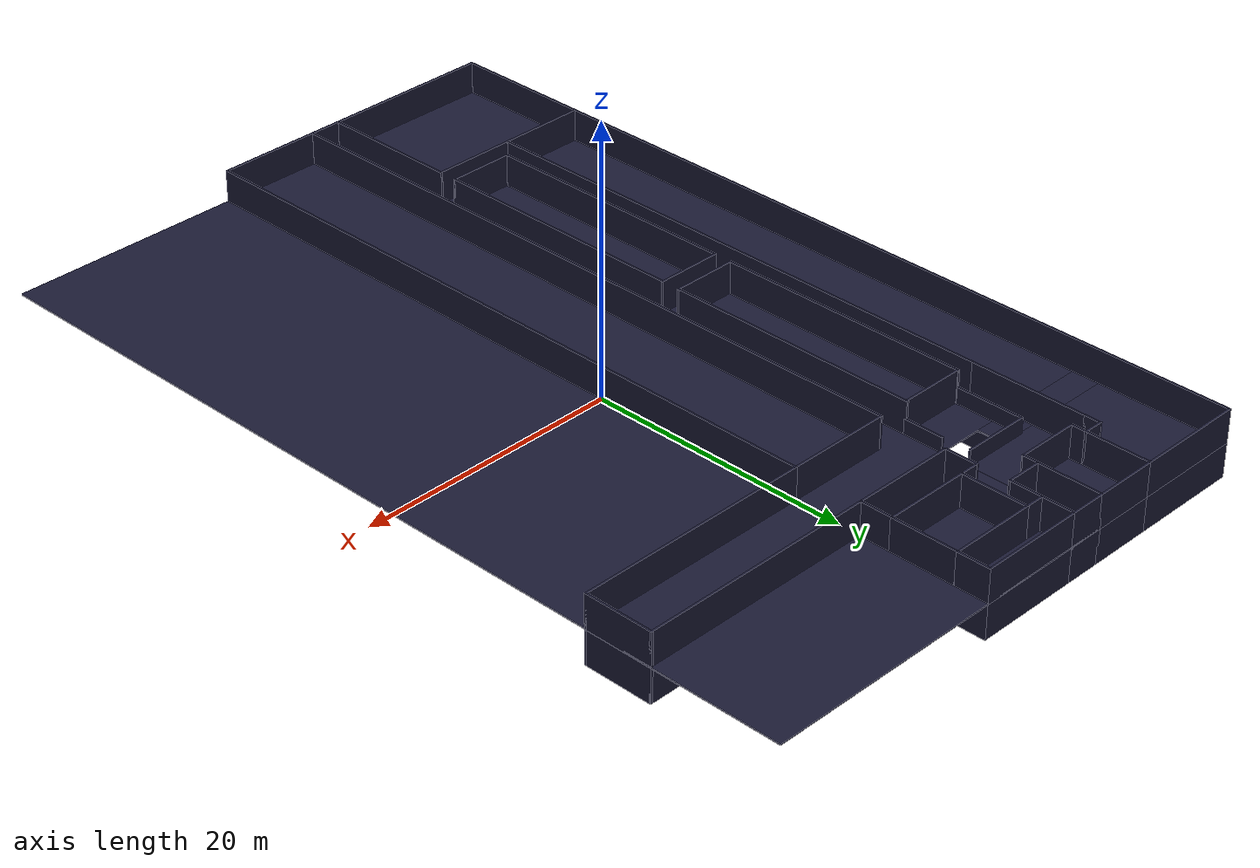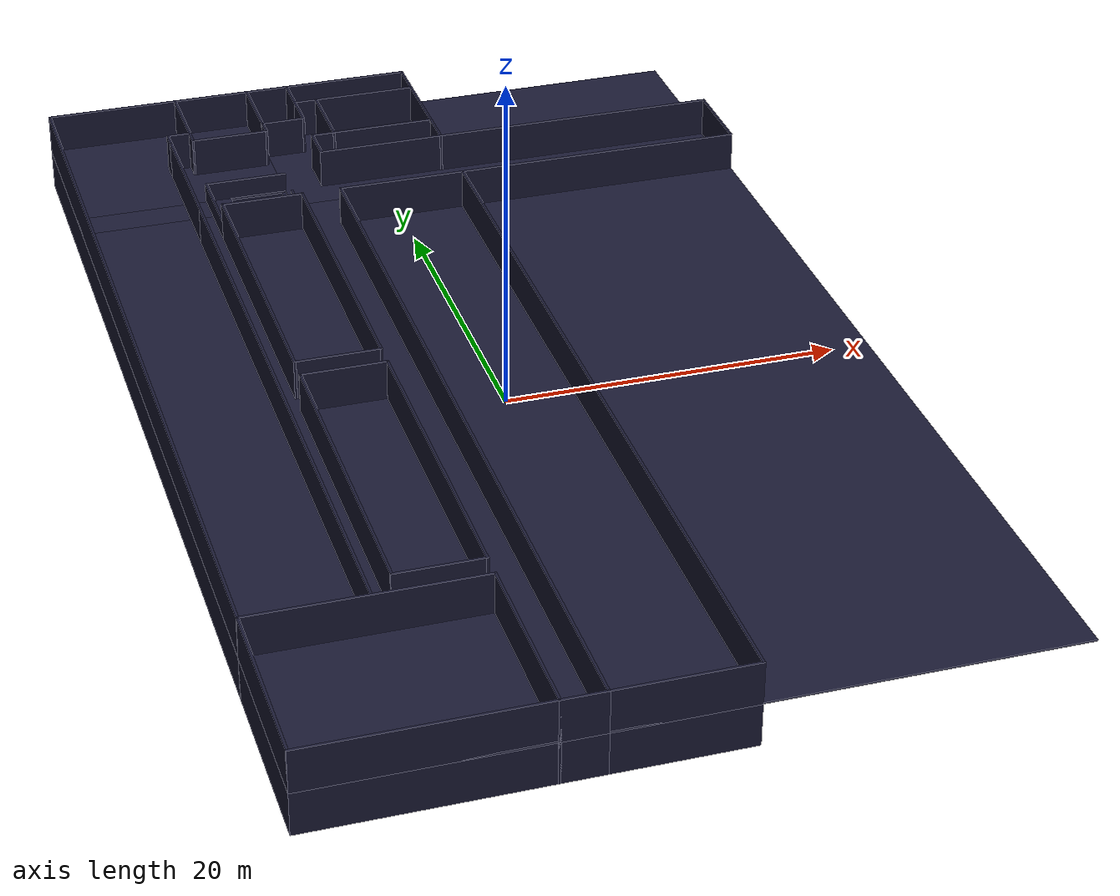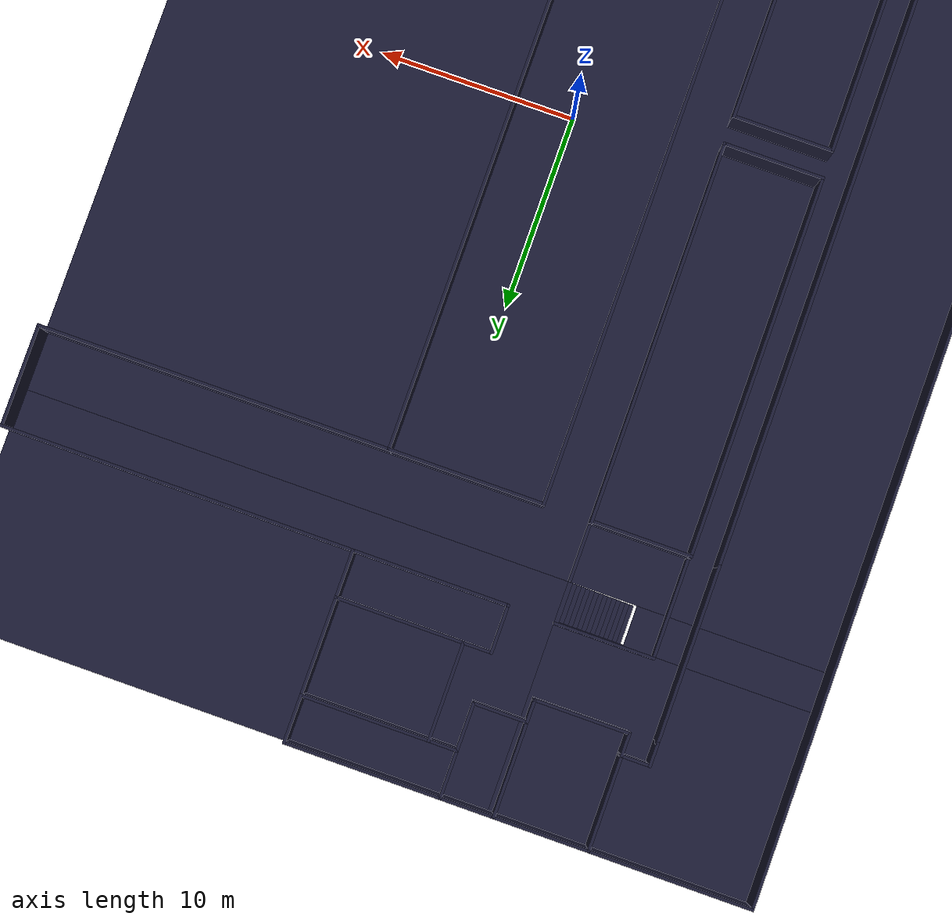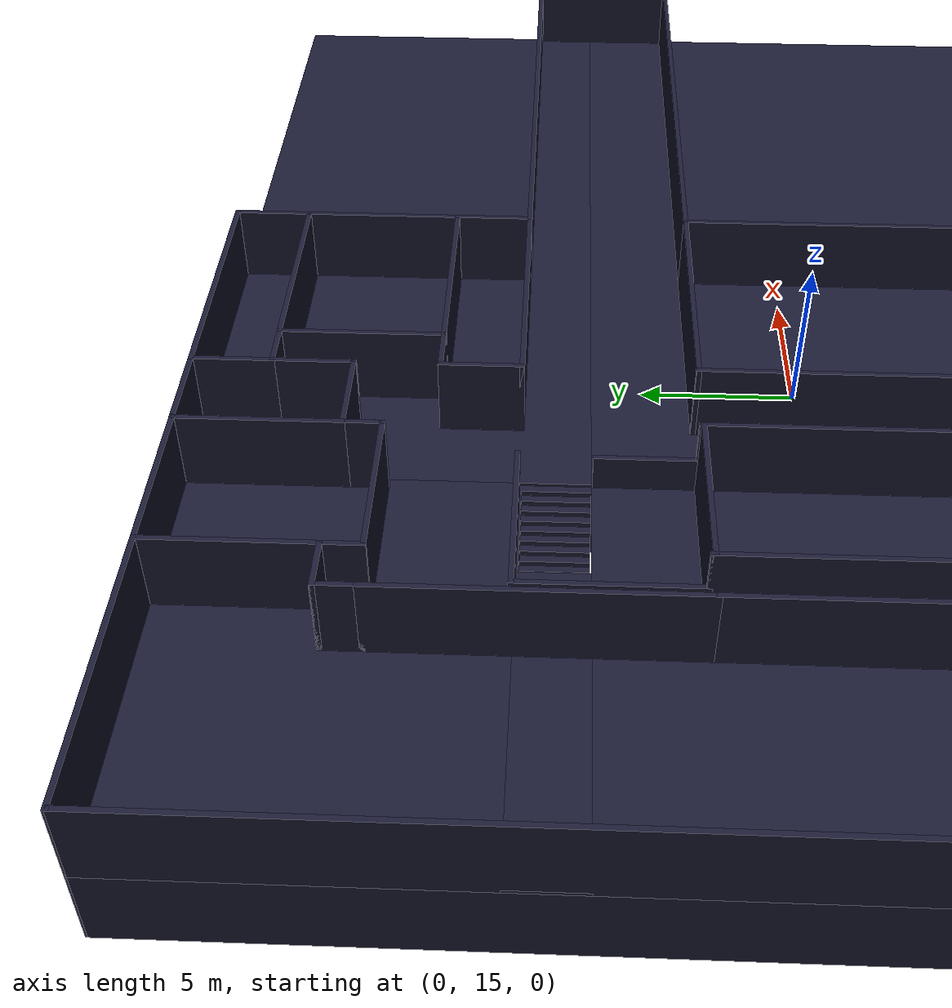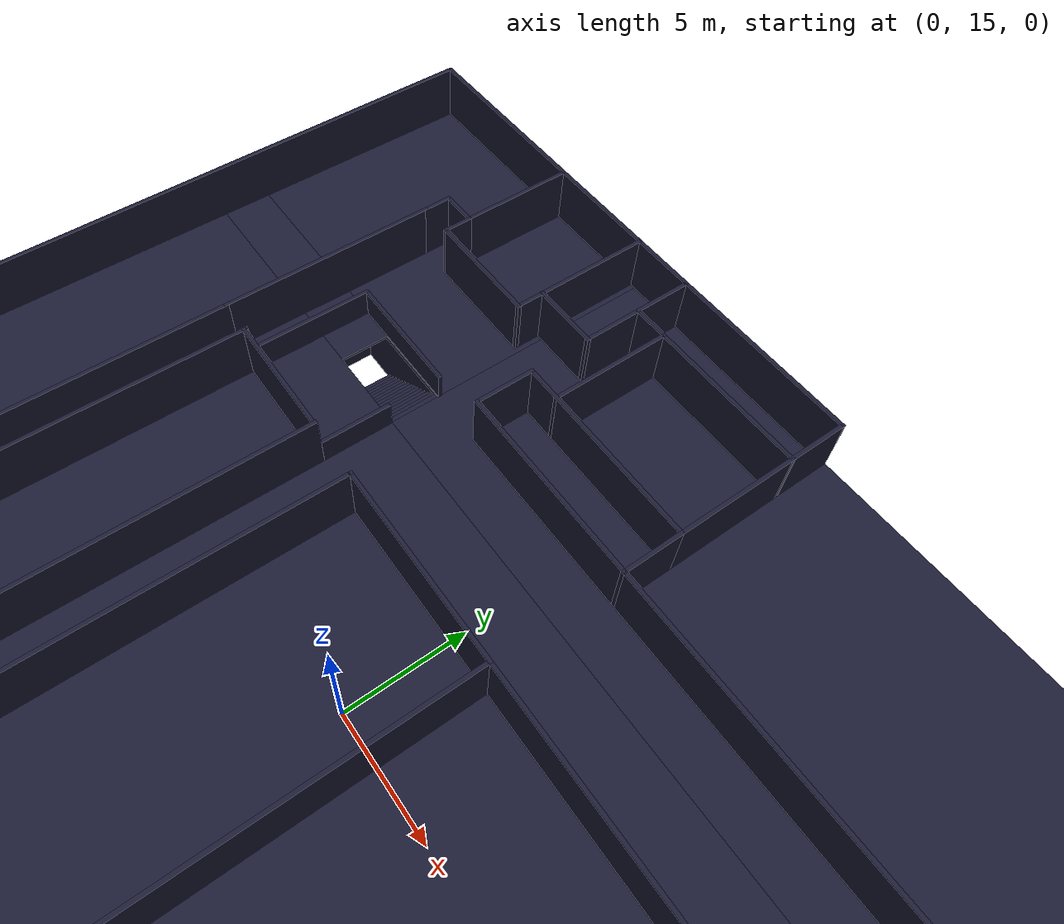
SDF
<sdf version="1.6">
 <world name="dinf_world">
  <physics name="1ms" type="ignored">
   <max_step_size>0.001</max_step_size>
   <real_time_factor>1.0</real_time_factor>
  </physics>
  <plugin filename="libignition-gazebo-physics-system.so" name="ignition::gazebo::systems::Physics"/>
  <plugin filename="libignition-gazebo-sensors-system.so" name="ignition::gazebo::systems::Sensors">
   <render_engine>ogre2</render_engine>
  </plugin>
  <plugin filename="libignition-gazebo-scene-broadcaster-system.so" name="ignition::gazebo::systems::SceneBroadcaster"/>
  <light type="directional" name="sun">
   <pose>0 0 10 0 0 0</pose>
   <diffuse>0.8 0.8 0.8 1</diffuse>
   <specular>0.2 0.2 0.2 1</specular>
   <attenuation>
    <range>1000</range>
    <constant>0.9</constant>
    <linear>0.01</linear>
    <quadratic>0.001</quadratic>
   </attenuation>
   <direction>-0.5 0.1 -0.9</direction>
  </light>
  <model name="ground_plane">
   <static>true</static>
   <link name="link">
    <collision name="collision"><geometry><box><size>20 20 0.1</size></box></geometry></collision>
    <visual name="visual">
     <geometry><box><size>20 20 0.1</size></box></geometry>
     <material>
      <ambient>0.8 0.8 0.8 1</ambient>
      <diffuse>0.8 0.8 0.8 1</diffuse>
      <specular>0.8 0.8 0.8 1</specular>
     </material>
    </visual>
   </link>
  </model>
  <include><pose>0 0 0 0 0 1.57</pose><uri>mode://2ndo_andar_passarela_escadas_v4</uri></include>
 </world>
</sdf>

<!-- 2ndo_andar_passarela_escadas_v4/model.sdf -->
<sdf version='1.7'>
  <model name='2ndo_andar_passarela_escadas_v4'>
    <pose>-4.9719 -7.73678 0 0 -0 0</pose>
    <link name='Floor_2'>
      <pose>0 0 2.5 0 -0 0</pose>
      <visual name='Floor_2_Visual_0'>
        <pose>-5.84149 0 0.05 0 -0 0</pose>
        <geometry>
          <box>
            <size>55.2168 40.95 0.1</size>
          </box>
        </geometry>
        <material>
          <script>
            <uri>file://media/materials/scripts/gazebo.material</uri>
            <name>Gazebo/Grey</name>
          </script>
          <ambient>0.1 0.1 0.1 1</ambient>
          <diffuse>0.1 0.1 0.2 1</diffuse>
          <specular>0 0 0 0</specular>
          <emissive>0 0 0 1</emissive>
        </material>
        <meta>
          <layer>1</layer>
        </meta>
      </visual>
      <collision name='Floor_2_Collision_0'>
        <geometry>
          <box>
            <size>55.2168 40.95 0.1</size>
          </box>
        </geometry>
        <pose>-5.84149 0 0.05 0 -0 0</pose>
      </collision>
      <visual name='Floor_2_Visual_1'>
        <pose>27.6084 -6.58012 0.05 0 -0 0</pose>
        <geometry>
          <box>
            <size>11.683 27.7898 0.1</size>
          </box>
        </geometry>
        <material>
          <script>
            <uri>file://media/materials/scripts/gazebo.material</uri>
            <name>Gazebo/Grey</name>
          </script>
          <ambient>0.1 0.1 0.1 1</ambient>
          <diffuse>0.1 0.1 0.2 1</diffuse>
          <specular>0 0 0 0</specular>
          <emissive>0 0 0 1</emissive>
        </material>
        <meta>
          <layer>1</layer>
        </meta>
      </visual>
      <collision name='Floor_2_Collision_1'>
        <geometry>
          <box>
            <size>11.683 27.7898 0.1</size>
          </box>
        </geometry>
        <pose>27.6084 -6.58012 0.05 0 -0 0</pose>
      </collision>
      <visual name='Floor_2_Visual_2'>
        <pose>28.6242 13.8949 0.05 0 -0 0</pose>
        <geometry>
          <box>
            <size>9.65136 13.1602 0.1</size>
          </box>
        </geometry>
        <material>
          <script>
            <uri>file://media/materials/scripts/gazebo.material</uri>
            <name>Gazebo/Grey</name>
          </script>
          <ambient>0.1 0.1 0.1 1</ambient>
          <diffuse>0.1 0.1 0.2 1</diffuse>
          <specular>0 0 0 0</specular>
          <emissive>0 0 0 1</emissive>
        </material>
        <meta>
          <layer>1</layer>
        </meta>
      </visual>
      <collision name='Floor_2_Collision_2'>
        <geometry>
          <box>
            <size>9.65136 13.1602 0.1</size>
          </box>
        </geometry>
        <pose>28.6242 13.8949 0.05 0 -0 0</pose>
      </collision>
      <visual name='Floor_2_Visual_3'>
        <pose>22.7827 15.6449 0.05 0 -0 0</pose>
        <geometry>
          <box>
            <size>2.03163 9.66024 0.1</size>
          </box>
        </geometry>
        <material>
          <script>
            <uri>file://media/materials/scripts/gazebo.material</uri>
            <name>Gazebo/Grey</name>
          </script>
          <ambient>0.1 0.1 0.1 1</ambient>
          <diffuse>0.1 0.1 0.2 1</diffuse>
          <specular>0 0 0 0</specular>
          <emissive>0 0 0 1</emissive>
        </material>
        <meta>
          <layer>1</layer>
        </meta>
      </visual>
      <collision name='Floor_2_Collision_3'>
        <geometry>
          <box>
            <size>2.03163 9.66024 0.1</size>
          </box>
        </geometry>
        <pose>22.7827 15.6449 0.05 0 -0 0</pose>
      </collision>
    </link>
    <link name='Stairs_1'>
      <visual name='Stairs_1_Visual_0'>
        <pose>22.7827 10.6981 0.083333 0 -0 0</pose>
        <geometry>
          <box>
            <size>2.03163 0.233333 0.166667</size>
          </box>
        </geometry>
        <material>
          <script>
            <uri>file://media/materials/scripts/gazebo.material</uri>
            <name>Gazebo/Grey</name>
          </script>
          <ambient>0.1 0.1 0.1 1</ambient>
          <diffuse>0.1 0.1 0.2 1</diffuse>
          <specular>0 0 0 0</specular>
          <emissive>0 0 0 1</emissive>
        </material>
        <meta>
          <layer>0</layer>
        </meta>
      </visual>
      <collision name='Stairs_1_Collision_0'>
        <geometry>
          <box>
            <size>2.03163 0.233333 0.166667</size>
          </box>
        </geometry>
        <pose>22.7827 10.6981 0.083333 0 -0 0</pose>
      </collision>
      <visual name='Stairs_1_Visual_1'>
        <pose>22.7827 10.4648 0.25 0 -0 0</pose>
        <geometry>
          <box>
            <size>2.03163 0.233333 0.166667</size>
          </box>
        </geometry>
        <material>
          <script>
            <uri>file://media/materials/scripts/gazebo.material</uri>
            <name>Gazebo/Grey</name>
          </script>
          <ambient>0.1 0.1 0.1 1</ambient>
          <diffuse>0.1 0.1 0.2 1</diffuse>
          <specular>0 0 0 0</specular>
          <emissive>0 0 0 1</emissive>
        </material>
        <meta>
          <layer>0</layer>
        </meta>
      </visual>
      <collision name='Stairs_1_Collision_1'>
        <geometry>
          <box>
            <size>2.03163 0.233333 0.166667</size>
          </box>
        </geometry>
        <pose>22.7827 10.4648 0.25 0 -0 0</pose>
      </collision>
      <visual name='Stairs_1_Visual_2'>
        <pose>22.7827 10.2314 0.416667 0 -0 0</pose>
        <geometry>
          <box>
            <size>2.03163 0.233333 0.166667</size>
          </box>
        </geometry>
        <material>
          <script>
            <uri>file://media/materials/scripts/gazebo.material</uri>
            <name>Gazebo/Grey</name>
          </script>
          <ambient>0.1 0.1 0.1 1</ambient>
          <diffuse>0.1 0.1 0.2 1</diffuse>
          <specular>0 0 0 0</specular>
          <emissive>0 0 0 1</emissive>
        </material>
        <meta>
          <layer>0</layer>
        </meta>
      </visual>
      <collision name='Stairs_1_Collision_2'>
        <geometry>
          <box>
            <size>2.03163 0.233333 0.166667</size>
          </box>
        </geometry>
        <pose>22.7827 10.2314 0.416667 0 -0 0</pose>
      </collision>
      <visual name='Stairs_1_Visual_3'>
        <pose>22.7827 9.99809 0.583333 0 -0 0</pose>
        <geometry>
          <box>
            <size>2.03163 0.233333 0.166667</size>
          </box>
        </geometry>
        <material>
          <script>
            <uri>file://media/materials/scripts/gazebo.material</uri>
            <name>Gazebo/Grey</name>
          </script>
          <ambient>0.1 0.1 0.1 1</ambient>
          <diffuse>0.1 0.1 0.2 1</diffuse>
          <specular>0 0 0 0</specular>
          <emissive>0 0 0 1</emissive>
        </material>
        <meta>
          <layer>0</layer>
        </meta>
      </visual>
      <collision name='Stairs_1_Collision_3'>
        <geometry>
          <box>
            <size>2.03163 0.233333 0.166667</size>
          </box>
        </geometry>
        <pose>22.7827 9.99809 0.583333 0 -0 0</pose>
      </collision>
      <visual name='Stairs_1_Visual_4'>
        <pose>22.7827 9.76476 0.75 0 -0 0</pose>
        <geometry>
          <box>
            <size>2.03163 0.233333 0.166667</size>
          </box>
        </geometry>
        <material>
          <script>
            <uri>file://media/materials/scripts/gazebo.material</uri>
            <name>Gazebo/Grey</name>
          </script>
          <ambient>0.1 0.1 0.1 1</ambient>
          <diffuse>0.1 0.1 0.2 1</diffuse>
          <specular>0 0 0 0</specular>
          <emissive>0 0 0 1</emissive>
        </material>
        <meta>
          <layer>0</layer>
        </meta>
      </visual>
      <collision name='Stairs_1_Collision_4'>
        <geometry>
          <box>
            <size>2.03163 0.233333 0.166667</size>
          </box>
        </geometry>
        <pose>22.7827 9.76476 0.75 0 -0 0</pose>
      </collision>
      <visual name='Stairs_1_Visual_5'>
        <pose>22.7827 9.53143 0.916667 0 -0 0</pose>
        <geometry>
          <box>
            <size>2.03163 0.233333 0.166667</size>
          </box>
        </geometry>
        <material>
          <script>
            <uri>file://media/materials/scripts/gazebo.material</uri>
            <name>Gazebo/Grey</name>
          </script>
          <ambient>0.1 0.1 0.1 1</ambient>
          <diffuse>0.1 0.1 0.2 1</diffuse>
          <specular>0 0 0 0</specular>
          <emissive>0 0 0 1</emissive>
        </material>
        <meta>
          <layer>0</layer>
        </meta>
      </visual>
      <collision name='Stairs_1_Collision_5'>
        <geometry>
          <box>
            <size>2.03163 0.233333 0.166667</size>
          </box>
        </geometry>
        <pose>22.7827 9.53143 0.916667 0 -0 0</pose>
      </collision>
      <visual name='Stairs_1_Visual_6'>
        <pose>22.7827 9.29809 1.08333 0 -0 0</pose>
        <geometry>
          <box>
            <size>2.03163 0.233333 0.166667</size>
          </box>
        </geometry>
        <material>
          <script>
            <uri>file://media/materials/scripts/gazebo.material</uri>
            <name>Gazebo/Grey</name>
          </script>
          <ambient>0.1 0.1 0.1 1</ambient>
          <diffuse>0.1 0.1 0.2 1</diffuse>
          <specular>0 0 0 0</specular>
          <emissive>0 0 0 1</emissive>
        </material>
        <meta>
          <layer>0</layer>
        </meta>
      </visual>
      <collision name='Stairs_1_Collision_6'>
        <geometry>
          <box>
            <size>2.03163 0.233333 0.166667</size>
          </box>
        </geometry>
        <pose>22.7827 9.29809 1.08333 0 -0 0</pose>
      </collision>
      <visual name='Stairs_1_Visual_7'>
        <pose>22.7827 9.06476 1.25 0 -0 0</pose>
        <geometry>
          <box>
            <size>2.03163 0.233333 0.166667</size>
          </box>
        </geometry>
        <material>
          <script>
            <uri>file://media/materials/scripts/gazebo.material</uri>
            <name>Gazebo/Grey</name>
          </script>
          <ambient>0.1 0.1 0.1 1</ambient>
          <diffuse>0.1 0.1 0.2 1</diffuse>
          <specular>0 0 0 0</specular>
          <emissive>0 0 0 1</emissive>
        </material>
        <meta>
          <layer>0</layer>
        </meta>
      </visual>
      <collision name='Stairs_1_Collision_7'>
        <geometry>
          <box>
            <size>2.03163 0.233333 0.166667</size>
          </box>
        </geometry>
        <pose>22.7827 9.06476 1.25 0 -0 0</pose>
      </collision>
      <visual name='Stairs_1_Visual_8'>
        <pose>22.7827 8.83143 1.41667 0 -0 0</pose>
        <geometry>
          <box>
            <size>2.03163 0.233333 0.166667</size>
          </box>
        </geometry>
        <material>
          <script>
            <uri>file://media/materials/scripts/gazebo.material</uri>
            <name>Gazebo/Grey</name>
          </script>
          <ambient>0.1 0.1 0.1 1</ambient>
          <diffuse>0.1 0.1 0.2 1</diffuse>
          <specular>0 0 0 0</specular>
          <emissive>0 0 0 1</emissive>
        </material>
        <meta>
          <layer>0</layer>
        </meta>
      </visual>
      <collision name='Stairs_1_Collision_8'>
        <geometry>
          <box>
            <size>2.03163 0.233333 0.166667</size>
          </box>
        </geometry>
        <pose>22.7827 8.83143 1.41667 0 -0 0</pose>
      </collision>
      <visual name='Stairs_1_Visual_9'>
        <pose>22.7827 8.59809 1.58333 0 -0 0</pose>
        <geometry>
          <box>
            <size>2.03163 0.233333 0.166667</size>
          </box>
        </geometry>
        <material>
          <script>
            <uri>file://media/materials/scripts/gazebo.material</uri>
            <name>Gazebo/Grey</name>
          </script>
          <ambient>0.1 0.1 0.1 1</ambient>
          <diffuse>0.1 0.1 0.2 1</diffuse>
          <specular>0 0 0 0</specular>
          <emissive>0 0 0 1</emissive>
        </material>
        <meta>
          <layer>0</layer>
        </meta>
      </visual>
      <collision name='Stairs_1_Collision_9'>
        <geometry>
          <box>
            <size>2.03163 0.233333 0.166667</size>
          </box>
        </geometry>
        <pose>22.7827 8.59809 1.58333 0 -0 0</pose>
      </collision>
      <visual name='Stairs_1_Visual_10'>
        <pose>22.7827 8.36476 1.75 0 -0 0</pose>
        <geometry>
          <box>
            <size>2.03163 0.233333 0.166667</size>
          </box>
        </geometry>
        <material>
          <script>
            <uri>file://media/materials/scripts/gazebo.material</uri>
            <name>Gazebo/Grey</name>
          </script>
          <ambient>0.1 0.1 0.1 1</ambient>
          <diffuse>0.1 0.1 0.2 1</diffuse>
          <specular>0 0 0 0</specular>
          <emissive>0 0 0 1</emissive>
        </material>
        <meta>
          <layer>0</layer>
        </meta>
      </visual>
      <collision name='Stairs_1_Collision_10'>
        <geometry>
          <box>
            <size>2.03163 0.233333 0.166667</size>
          </box>
        </geometry>
        <pose>22.7827 8.36476 1.75 0 -0 0</pose>
      </collision>
      <visual name='Stairs_1_Visual_11'>
        <pose>22.7827 8.13143 1.91667 0 -0 0</pose>
        <geometry>
          <box>
            <size>2.03163 0.233333 0.166667</size>
          </box>
        </geometry>
        <material>
          <script>
            <uri>file://media/materials/scripts/gazebo.material</uri>
            <name>Gazebo/Grey</name>
          </script>
          <ambient>0.1 0.1 0.1 1</ambient>
          <diffuse>0.1 0.1 0.2 1</diffuse>
          <specular>0 0 0 0</specular>
          <emissive>0 0 0 1</emissive>
        </material>
        <meta>
          <layer>0</layer>
        </meta>
      </visual>
      <collision name='Stairs_1_Collision_11'>
        <geometry>
          <box>
            <size>2.03163 0.233333 0.166667</size>
          </box>
        </geometry>
        <pose>22.7827 8.13143 1.91667 0 -0 0</pose>
      </collision>
      <visual name='Stairs_1_Visual_12'>
        <pose>22.7827 7.89809 2.08333 0 -0 0</pose>
        <geometry>
          <box>
            <size>2.03163 0.233333 0.166667</size>
          </box>
        </geometry>
        <material>
          <script>
            <uri>file://media/materials/scripts/gazebo.material</uri>
            <name>Gazebo/Grey</name>
          </script>
          <ambient>0.1 0.1 0.1 1</ambient>
          <diffuse>0.1 0.1 0.2 1</diffuse>
          <specular>0 0 0 0</specular>
          <emissive>0 0 0 1</emissive>
        </material>
        <meta>
          <layer>0</layer>
        </meta>
      </visual>
      <collision name='Stairs_1_Collision_12'>
        <geometry>
          <box>
            <size>2.03163 0.233333 0.166667</size>
          </box>
        </geometry>
        <pose>22.7827 7.89809 2.08333 0 -0 0</pose>
      </collision>
      <visual name='Stairs_1_Visual_13'>
        <pose>22.7827 7.66476 2.25 0 -0 0</pose>
        <geometry>
          <box>
            <size>2.03163 0.233333 0.166667</size>
          </box>
        </geometry>
        <material>
          <script>
            <uri>file://media/materials/scripts/gazebo.material</uri>
            <name>Gazebo/Grey</name>
          </script>
          <ambient>0.1 0.1 0.1 1</ambient>
          <diffuse>0.1 0.1 0.2 1</diffuse>
          <specular>0 0 0 0</specular>
          <emissive>0 0 0 1</emissive>
        </material>
        <meta>
          <layer>0</layer>
        </meta>
      </visual>
      <collision name='Stairs_1_Collision_13'>
        <geometry>
          <box>
            <size>2.03163 0.233333 0.166667</size>
          </box>
        </geometry>
        <pose>22.7827 7.66476 2.25 0 -0 0</pose>
      </collision>
      <visual name='Stairs_1_Visual_14'>
        <pose>22.7827 7.43143 2.41667 0 -0 0</pose>
        <geometry>
          <box>
            <size>2.03163 0.233333 0.166667</size>
          </box>
        </geometry>
        <material>
          <script>
            <uri>file://media/materials/scripts/gazebo.material</uri>
            <name>Gazebo/Grey</name>
          </script>
          <ambient>0.1 0.1 0.1 1</ambient>
          <diffuse>0.1 0.1 0.2 1</diffuse>
          <specular>0 0 0 0</specular>
          <emissive>0 0 0 1</emissive>
        </material>
        <meta>
          <layer>0</layer>
        </meta>
      </visual>
      <collision name='Stairs_1_Collision_14'>
        <geometry>
          <box>
            <size>2.03163 0.233333 0.166667</size>
          </box>
        </geometry>
        <pose>22.7827 7.43143 2.41667 0 -0 0</pose>
      </collision>
    </link>
    <link name='Wall_0'>
      <collision name='Wall_0_Collision'>
        <geometry>
          <box>
            <size>52.3 0.15 2.5</size>
          </box>
        </geometry>
        <pose>0 0 1.25 0 -0 0</pose>
      </collision>
      <visual name='Wall_0_Visual'>
        <pose>0 0 1.25 0 -0 0</pose>
        <geometry>
          <box>
            <size>52.3 0.15 2.5</size>
          </box>
        </geometry>
        <material>
          <script>
            <uri>file://media/materials/scripts/gazebo.material</uri>
            <name>Gazebo/Grey</name>
          </script>
          <ambient>0.1 0.1 0.1 1</ambient>
          <diffuse>0.1 0.1 0.2 1</diffuse>
          <specular>0 0 0 0</specular>
          <emissive>0 0 0 1</emissive>
        </material>
        <meta>
          <layer>0</layer>
        </meta>
      </visual>
      <pose>-7.2999 -2.8 0 0 -0 0</pose>
    </link>
    <link name='Wall_101'>
      <collision name='Wall_101_Collision'>
        <geometry>
          <box>
            <size>4.75 0.15 2.5</size>
          </box>
        </geometry>
        <pose>0 0 1.25 0 -0 0</pose>
      </collision>
      <visual name='Wall_101_Visual'>
        <pose>0 0 1.25 0 -0 0</pose>
        <geometry>
          <box>
            <size>4.75 0.15 2.5</size>
          </box>
        </geometry>
        <material>
          <script>
            <uri>file://media/materials/scripts/gazebo.material</uri>
            <name>Gazebo/Grey</name>
          </script>
          <ambient>0.1 0.1 0.1 1</ambient>
          <diffuse>0.1 0.1 0.2 1</diffuse>
          <specular>0 0 0 0</specular>
          <emissive>0 0 0 1</emissive>
        </material>
        <meta>
          <layer>0</layer>
        </meta>
      </visual>
      <pose>33.3749 9.84978 0 0 -0 1.5708</pose>
    </link>
    <link name='Wall_103'>
      <collision name='Wall_103_Collision'>
        <geometry>
          <box>
            <size>4.85 0.15 2.5</size>
          </box>
        </geometry>
        <pose>0 0 1.25 0 -0 0</pose>
      </collision>
      <visual name='Wall_103_Visual'>
        <pose>0 0 1.25 0 -0 0</pose>
        <geometry>
          <box>
            <size>4.85 0.15 2.5</size>
          </box>
        </geometry>
        <material>
          <script>
            <uri>file://media/materials/scripts/gazebo.material</uri>
            <name>Gazebo/Grey</name>
          </script>
          <ambient>0.1 0.1 0.1 1</ambient>
          <diffuse>0.1 0.1 0.2 1</diffuse>
          <specular>0 0 0 0</specular>
          <emissive>0 0 0 1</emissive>
        </material>
        <meta>
          <layer>0</layer>
        </meta>
      </visual>
      <pose>31.0249 12.2998 0 0 -0 0</pose>
    </link>
    <link name='Wall_109'>
      <collision name='Wall_109_Collision'>
        <geometry>
          <box>
            <size>5.2 0.15 2.5</size>
          </box>
        </geometry>
        <pose>0 0 1.25 0 -0 0</pose>
      </collision>
      <visual name='Wall_109_Visual'>
        <pose>0 0 1.25 0 -0 0</pose>
        <geometry>
          <box>
            <size>5.2 0.15 2.5</size>
          </box>
        </geometry>
        <material>
          <script>
            <uri>file://media/materials/scripts/gazebo.material</uri>
            <name>Gazebo/Grey</name>
          </script>
          <ambient>0.1 0.1 0.1 1</ambient>
          <diffuse>0.1 0.1 0.2 1</diffuse>
          <specular>0 0 0 0</specular>
          <emissive>0 0 0 1</emissive>
        </material>
        <meta>
          <layer>0</layer>
        </meta>
      </visual>
      <pose>21.3001 7.35 0 0 -0 0</pose>
    </link>
    <link name='Wall_111'>
      <collision name='Wall_111_Collision'>
        <geometry>
          <box>
            <size>5.1 0.15 2.5</size>
          </box>
        </geometry>
        <pose>0 0 1.25 0 -0 0</pose>
      </collision>
      <visual name='Wall_111_Visual'>
        <pose>0 0 1.25 0 -0 0</pose>
        <geometry>
          <box>
            <size>5.1 0.15 2.5</size>
          </box>
        </geometry>
        <material>
          <script>
            <uri>file://media/materials/scripts/gazebo.material</uri>
            <name>Gazebo/Grey</name>
          </script>
          <ambient>0.1 0.1 0.1 1</ambient>
          <diffuse>0.1 0.1 0.2 1</diffuse>
          <specular>0 0 0 0</specular>
          <emissive>0 0 0 1</emissive>
        </material>
        <meta>
          <layer>0</layer>
        </meta>
      </visual>
      <pose>23.8251 9.825 0 0 -0 1.5708</pose>
    </link>
    <link name='Wall_113'>
      <collision name='Wall_113_Collision'>
        <geometry>
          <box>
            <size>5.2002 0.15 2.5</size>
          </box>
        </geometry>
        <pose>0 0 1.25 0 -0 0</pose>
      </collision>
      <visual name='Wall_113_Visual'>
        <pose>0 0 1.25 0 -0 0</pose>
        <geometry>
          <box>
            <size>5.2002 0.15 2.5</size>
          </box>
        </geometry>
        <material>
          <script>
            <uri>file://media/materials/scripts/gazebo.material</uri>
            <name>Gazebo/Grey</name>
          </script>
          <ambient>0.1 0.1 0.1 1</ambient>
          <diffuse>0.1 0.1 0.2 1</diffuse>
          <specular>0 0 0 0</specular>
          <emissive>0 0 0 1</emissive>
        </material>
        <meta>
          <layer>0</layer>
        </meta>
      </visual>
      <pose>21.3 12.2999 0 0 -0 -3.14155</pose>
    </link>
    <link name='Wall_118'>
      <collision name='Wall_118_Collision'>
        <geometry>
          <box>
            <size>13.2 0.15 2.5</size>
          </box>
        </geometry>
        <pose>0 0 1.25 0 -0 0</pose>
      </collision>
      <visual name='Wall_118_Visual'>
        <pose>0 0 1.25 0 -0 0</pose>
        <geometry>
          <box>
            <size>13.2 0.15 2.5</size>
          </box>
        </geometry>
        <material>
          <script>
            <uri>file://media/materials/scripts/gazebo.material</uri>
            <name>Gazebo/Grey</name>
          </script>
          <ambient>0.1 0.1 0.1 1</ambient>
          <diffuse>0.1 0.1 0.2 1</diffuse>
          <specular>0 0 0 0</specular>
          <emissive>0 0 0 1</emissive>
        </material>
        <meta>
          <layer>0</layer>
        </meta>
      </visual>
      <pose>-33.3749 13.875 0 0 -0 1.5708</pose>
    </link>
    <link name='Wall_120'>
      <collision name='Wall_120_Collision'>
        <geometry>
          <box>
            <size>10.8 0.15 2.5</size>
          </box>
        </geometry>
        <pose>0 0 1.25 0 -0 0</pose>
      </collision>
      <visual name='Wall_120_Visual'>
        <pose>0 0 1.25 0 -0 0</pose>
        <geometry>
          <box>
            <size>10.8 0.15 2.5</size>
          </box>
        </geometry>
        <material>
          <script>
            <uri>file://media/materials/scripts/gazebo.material</uri>
            <name>Gazebo/Grey</name>
          </script>
          <ambient>0.1 0.1 0.1 1</ambient>
          <diffuse>0.1 0.1 0.2 1</diffuse>
          <specular>0 0 0 0</specular>
          <emissive>0 0 0 1</emissive>
        </material>
        <meta>
          <layer>0</layer>
        </meta>
      </visual>
      <pose>-28.0499 20.4 0 0 -0 0</pose>
    </link>
    <link name='Wall_123'>
      <collision name='Wall_123_Collision'>
        <geometry>
          <box>
            <size>13.2 0.15 2.5</size>
          </box>
        </geometry>
        <pose>0 0 1.25 0 -0 0</pose>
      </collision>
      <visual name='Wall_123_Visual'>
        <pose>0 0 1.25 0 -0 0</pose>
        <geometry>
          <box>
            <size>13.2 0.15 2.5</size>
          </box>
        </geometry>
        <material>
          <script>
            <uri>file://media/materials/scripts/gazebo.material</uri>
            <name>Gazebo/Grey</name>
          </script>
          <ambient>0.1 0.1 0.1 1</ambient>
          <diffuse>0.1 0.1 0.2 1</diffuse>
          <specular>0 0 0 0</specular>
          <emissive>0 0 0 1</emissive>
        </material>
        <meta>
          <layer>0</layer>
        </meta>
      </visual>
      <pose>-22.7249 13.875 0 0 -0 -1.5708</pose>
    </link>
    <link name='Wall_125'>
      <collision name='Wall_125_Collision'>
        <geometry>
          <box>
            <size>10.8 0.15 2.5</size>
          </box>
        </geometry>
        <pose>0 0 1.25 0 -0 0</pose>
      </collision>
      <visual name='Wall_125_Visual'>
        <pose>0 0 1.25 0 -0 0</pose>
        <geometry>
          <box>
            <size>10.8 0.15 2.5</size>
          </box>
        </geometry>
        <material>
          <script>
            <uri>file://media/materials/scripts/gazebo.material</uri>
            <name>Gazebo/Grey</name>
          </script>
          <ambient>0.1 0.1 0.1 1</ambient>
          <diffuse>0.1 0.1 0.2 1</diffuse>
          <specular>0 0 0 0</specular>
          <emissive>0 0 0 1</emissive>
        </material>
        <meta>
          <layer>0</layer>
        </meta>
      </visual>
      <pose>-28.0499 7.35 0 0 -0 3.14159</pose>
    </link>
    <link name='Wall_129'>
      <collision name='Wall_129_Collision'>
        <geometry>
          <box>
            <size>19.8 0.15 2.5</size>
          </box>
        </geometry>
        <pose>0 0 1.25 0 -0 0</pose>
      </collision>
      <visual name='Wall_129_Visual'>
        <pose>0 0 1.25 0 -0 0</pose>
        <geometry>
          <box>
            <size>19.8 0.15 2.5</size>
          </box>
        </geometry>
        <material>
          <script>
            <uri>file://media/materials/scripts/gazebo.material</uri>
            <name>Gazebo/Grey</name>
          </script>
          <ambient>0.1 0.1 0.1 1</ambient>
          <diffuse>0.1 0.1 0.2 1</diffuse>
          <specular>0 0 0 0</specular>
          <emissive>0 0 0 1</emissive>
        </material>
        <meta>
          <layer>0</layer>
        </meta>
      </visual>
      <pose>-11.4999 7.35 0 0 -0 0</pose>
    </link>
    <link name='Wall_132'>
      <collision name='Wall_132_Collision'>
        <geometry>
          <box>
            <size>5.1 0.15 2.5</size>
          </box>
        </geometry>
        <pose>0 0 1.25 0 -0 0</pose>
      </collision>
      <visual name='Wall_132_Visual'>
        <pose>0 0 1.25 0 -0 0</pose>
        <geometry>
          <box>
            <size>5.1 0.15 2.5</size>
          </box>
        </geometry>
        <material>
          <script>
            <uri>file://media/materials/scripts/gazebo.material</uri>
            <name>Gazebo/Grey</name>
          </script>
          <ambient>0.1 0.1 0.1 1</ambient>
          <diffuse>0.1 0.1 0.2 1</diffuse>
          <specular>0 0 0 0</specular>
          <emissive>0 0 0 1</emissive>
        </material>
        <meta>
          <layer>0</layer>
        </meta>
      </visual>
      <pose>-1.6749 9.825 0 0 -0 1.5708</pose>
    </link>
    <link name='Wall_134'>
      <collision name='Wall_134_Collision'>
        <geometry>
          <box>
            <size>5.1 0.15 2.5</size>
          </box>
        </geometry>
        <pose>0 0 1.25 0 -0 0</pose>
      </collision>
      <visual name='Wall_134_Visual'>
        <pose>0 0 1.25 0 -0 0</pose>
        <geometry>
          <box>
            <size>5.1 0.15 2.5</size>
          </box>
        </geometry>
        <material>
          <script>
            <uri>file://media/materials/scripts/gazebo.material</uri>
            <name>Gazebo/Grey</name>
          </script>
          <ambient>0.1 0.1 0.1 1</ambient>
          <diffuse>0.1 0.1 0.2 1</diffuse>
          <specular>0 0 0 0</specular>
          <emissive>0 0 0 1</emissive>
        </material>
        <meta>
          <layer>0</layer>
        </meta>
      </visual>
      <pose>-21.3249 9.825 0 0 -0 1.5708</pose>
    </link>
    <link name='Wall_136'>
      <collision name='Wall_136_Collision'>
        <geometry>
          <box>
            <size>19.75 0.15 2.5</size>
          </box>
        </geometry>
        <pose>0 0 1.25 0 -0 0</pose>
      </collision>
      <visual name='Wall_136_Visual'>
        <pose>0 0 1.25 0 -0 0</pose>
        <geometry>
          <box>
            <size>19.75 0.15 2.5</size>
          </box>
        </geometry>
        <material>
          <script>
            <uri>file://media/materials/scripts/gazebo.material</uri>
            <name>Gazebo/Grey</name>
          </script>
          <ambient>0.1 0.1 0.1 1</ambient>
          <diffuse>0.1 0.1 0.2 1</diffuse>
          <specular>0 0 0 0</specular>
          <emissive>0 0 0 1</emissive>
        </material>
        <meta>
          <layer>0</layer>
        </meta>
      </visual>
      <pose>-11.5249 12.3 0 0 -0 0</pose>
    </link>
    <link name='Wall_140'>
      <collision name='Wall_140_Collision'>
        <geometry>
          <box>
            <size>19.25 0.15 2.5</size>
          </box>
        </geometry>
        <pose>0 0 1.25 0 -0 0</pose>
      </collision>
      <visual name='Wall_140_Visual'>
        <pose>0 0 1.25 0 -0 0</pose>
        <geometry>
          <box>
            <size>19.25 0.15 2.5</size>
          </box>
        </geometry>
        <material>
          <script>
            <uri>file://media/materials/scripts/gazebo.material</uri>
            <name>Gazebo/Grey</name>
          </script>
          <ambient>0.1 0.1 0.1 1</ambient>
          <diffuse>0.1 0.1 0.2 1</diffuse>
          <specular>0 0 0 0</specular>
          <emissive>0 0 0 1</emissive>
        </material>
        <meta>
          <layer>0</layer>
        </meta>
      </visual>
      <pose>9.2751 7.35 0 0 -0 0</pose>
    </link>
    <link name='Wall_142'>
      <collision name='Wall_142_Collision'>
        <geometry>
          <box>
            <size>5.1 0.15 2.5</size>
          </box>
        </geometry>
        <pose>0 0 1.25 0 -0 0</pose>
      </collision>
      <visual name='Wall_142_Visual'>
        <pose>0 0 1.25 0 -0 0</pose>
        <geometry>
          <box>
            <size>5.1 0.15 2.5</size>
          </box>
        </geometry>
        <material>
          <script>
            <uri>file://media/materials/scripts/gazebo.material</uri>
            <name>Gazebo/Grey</name>
          </script>
          <ambient>0.1 0.1 0.1 1</ambient>
          <diffuse>0.1 0.1 0.2 1</diffuse>
          <specular>0 0 0 0</specular>
          <emissive>0 0 0 1</emissive>
        </material>
        <meta>
          <layer>0</layer>
        </meta>
      </visual>
      <pose>-0.274901 9.825 0 0 -0 1.5708</pose>
    </link>
    <link name='Wall_144'>
      <collision name='Wall_144_Collision'>
        <geometry>
          <box>
            <size>19.25 0.15 2.5</size>
          </box>
        </geometry>
        <pose>0 0 1.25 0 -0 0</pose>
      </collision>
      <visual name='Wall_144_Visual'>
        <pose>0 0 1.25 0 -0 0</pose>
        <geometry>
          <box>
            <size>19.25 0.15 2.5</size>
          </box>
        </geometry>
        <material>
          <script>
            <uri>file://media/materials/scripts/gazebo.material</uri>
            <name>Gazebo/Grey</name>
          </script>
          <ambient>0.1 0.1 0.1 1</ambient>
          <diffuse>0.1 0.1 0.2 1</diffuse>
          <specular>0 0 0 0</specular>
          <emissive>0 0 0 1</emissive>
        </material>
        <meta>
          <layer>0</layer>
        </meta>
      </visual>
      <pose>9.2751 12.3 0 0 -0 0</pose>
    </link>
    <link name='Wall_146'>
      <collision name='Wall_146_Collision'>
        <geometry>
          <box>
            <size>41.5 0.15 2.5</size>
          </box>
        </geometry>
        <pose>0 0 1.25 0 -0 0</pose>
      </collision>
      <visual name='Wall_146_Visual'>
        <pose>0 0 1.25 0 -0 0</pose>
        <geometry>
          <box>
            <size>41.5 0.15 2.5</size>
          </box>
        </geometry>
        <material>
          <script>
            <uri>file://media/materials/scripts/gazebo.material</uri>
            <name>Gazebo/Grey</name>
          </script>
          <ambient>0.1 0.1 0.1 1</ambient>
          <diffuse>0.1 0.1 0.2 1</diffuse>
          <specular>0 0 0 0</specular>
          <emissive>0 0 0 1</emissive>
        </material>
        <meta>
          <layer>0</layer>
        </meta>
      </visual>
      <pose>-1.9001 13.6998 0 0 -0 3.14159</pose>
    </link>
    <link name='Wall_150'>
      <collision name='Wall_150_Collision'>
        <geometry>
          <box>
            <size>56.2 0.15 2.5</size>
          </box>
        </geometry>
        <pose>0 0 1.25 0 -0 0</pose>
      </collision>
      <visual name='Wall_150_Visual'>
        <pose>0 0 1.25 0 -0 0</pose>
        <geometry>
          <box>
            <size>56.2 0.15 2.5</size>
          </box>
        </geometry>
        <material>
          <script>
            <uri>file://media/materials/scripts/gazebo.material</uri>
            <name>Gazebo/Grey</name>
          </script>
          <ambient>0.1 0.1 0.1 1</ambient>
          <diffuse>0.1 0.1 0.2 1</diffuse>
          <specular>0 0 0 0</specular>
          <emissive>0 0 0 1</emissive>
        </material>
        <meta>
          <layer>0</layer>
        </meta>
      </visual>
      <pose>5.3001 20.4 0 0 -0 0</pose>
    </link>
    <link name='Wall_152'>
      <collision name='Wall_152_Collision'>
        <geometry>
          <box>
            <size>8.25 0.15 2.5</size>
          </box>
        </geometry>
        <pose>0 0 1.25 0 -0 0</pose>
      </collision>
      <visual name='Wall_152_Visual'>
        <pose>0 0 1.25 0 -0 0</pose>
        <geometry>
          <box>
            <size>8.25 0.15 2.5</size>
          </box>
        </geometry>
        <material>
          <script>
            <uri>file://media/materials/scripts/gazebo.material</uri>
            <name>Gazebo/Grey</name>
          </script>
          <ambient>0.1 0.1 0.1 1</ambient>
          <diffuse>0.1 0.1 0.2 1</diffuse>
          <specular>0 0 0 0</specular>
          <emissive>0 0 0 1</emissive>
        </material>
        <meta>
          <layer>0</layer>
        </meta>
      </visual>
      <pose>33.3749 16.3498 0 0 -0 1.5708</pose>
    </link>
    <link name='Wall_154'>
      <collision name='Wall_154_Collision'>
        <geometry>
          <box>
            <size>17.75 0.15 2.5</size>
          </box>
        </geometry>
        <pose>0 0 1.25 0 -0 0</pose>
      </collision>
      <visual name='Wall_154_Visual'>
        <pose>0 0 1.25 0 -0 0</pose>
        <geometry>
          <box>
            <size>17.75 0.15 2.5</size>
          </box>
        </geometry>
        <material>
          <script>
            <uri>file://media/materials/scripts/gazebo.material</uri>
            <name>Gazebo/Grey</name>
          </script>
          <ambient>0.1 0.1 0.1 1</ambient>
          <diffuse>0.1 0.1 0.2 1</diffuse>
          <specular>0 0 0 0</specular>
          <emissive>0 0 0 1</emissive>
        </material>
        <meta>
          <layer>0</layer>
        </meta>
      </visual>
      <pose>18.7751 -11.6 0 0 -0 -1.5708</pose>
    </link>
    <link name='Wall_156'>
      <collision name='Wall_156_Collision'>
        <geometry>
          <box>
            <size>17.75 0.15 2.5</size>
          </box>
        </geometry>
        <pose>0 0 1.25 0 -0 0</pose>
      </collision>
      <visual name='Wall_156_Visual'>
        <pose>0 0 1.25 0 -0 0</pose>
        <geometry>
          <box>
            <size>17.75 0.15 2.5</size>
          </box>
        </geometry>
        <material>
          <script>
            <uri>file://media/materials/scripts/gazebo.material</uri>
            <name>Gazebo/Grey</name>
          </script>
          <ambient>0.1 0.1 0.1 1</ambient>
          <diffuse>0.1 0.1 0.2 1</diffuse>
          <specular>0 0 0 0</specular>
          <emissive>0 0 0 1</emissive>
        </material>
        <meta>
          <layer>0</layer>
        </meta>
      </visual>
      <pose>23.8251 -11.6 0 0 -0 -1.5708</pose>
    </link>
    <link name='Wall_159'>
      <collision name='Wall_159_Collision'>
        <geometry>
          <box>
            <size>5.2 0.15 2.5</size>
          </box>
        </geometry>
        <pose>0 0 1.25 0 -0 0</pose>
      </collision>
      <visual name='Wall_159_Visual'>
        <pose>0 0 1.25 0 -0 0</pose>
        <geometry>
          <box>
            <size>5.2 0.15 2.5</size>
          </box>
        </geometry>
        <material>
          <script>
            <uri>file://media/materials/scripts/gazebo.material</uri>
            <name>Gazebo/Grey</name>
          </script>
          <ambient>0.1 0.1 0.1 1</ambient>
          <diffuse>0.1 0.1 0.2 1</diffuse>
          <specular>0 0 0 0</specular>
          <emissive>0 0 0 1</emissive>
        </material>
        <meta>
          <layer>0</layer>
        </meta>
      </visual>
      <pose>21.3001 -20.4 0 0 -0 0</pose>
    </link>
    <link name='Wall_16'>
      <collision name='Wall_16_Collision'>
        <geometry>
          <box>
            <size>7.9 0.15 2.5</size>
          </box>
        </geometry>
        <pose>0 0 1.25 0 -0 0</pose>
      </collision>
      <visual name='Wall_16_Visual'>
        <pose>0 0 1.25 0 -0 0</pose>
        <geometry>
          <box>
            <size>7.9 0.15 2.5</size>
          </box>
        </geometry>
        <material>
          <script>
            <uri>file://media/materials/scripts/gazebo.material</uri>
            <name>Gazebo/Grey</name>
          </script>
          <ambient>0.1 0.1 0.1 1</ambient>
          <diffuse>0.1 0.1 0.2 1</diffuse>
          <specular>0 0 0 0</specular>
          <emissive>0 0 0 1</emissive>
        </material>
        <meta>
          <layer>0</layer>
        </meta>
      </visual>
      <pose>23.8251 1.075 0 0 -0 1.5708</pose>
    </link>
    <link name='Wall_162'>
      <collision name='Wall_162_Collision'>
        <geometry>
          <box>
            <size>2.55 0.15 2.5</size>
          </box>
        </geometry>
        <pose>0 0 1.25 0 -0 0</pose>
      </collision>
      <visual name='Wall_162_Visual'>
        <pose>0 0 1.25 0 -0 0</pose>
        <geometry>
          <box>
            <size>2.55 0.15 2.5</size>
          </box>
        </geometry>
        <material>
          <script>
            <uri>file://media/materials/scripts/gazebo.material</uri>
            <name>Gazebo/Grey</name>
          </script>
          <ambient>0.1 0.1 0.1 1</ambient>
          <diffuse>0.1 0.1 0.2 1</diffuse>
          <specular>0 0 0 0</specular>
          <emissive>0 0 0 1</emissive>
        </material>
        <meta>
          <layer>0</layer>
        </meta>
      </visual>
      <pose>-33.3749 6.15 0 0 -0 -1.5708</pose>
    </link>
    <link name='Wall_19'>
      <collision name='Wall_19_Collision'>
        <geometry>
          <box>
            <size>2.5 0.15 2.5</size>
          </box>
        </geometry>
        <pose>0 0 1.25 0 -0 0</pose>
      </collision>
      <visual name='Wall_19_Visual'>
        <pose>0 0 1.25 0 -0 0</pose>
        <geometry>
          <box>
            <size>2.5 0.15 2.5</size>
          </box>
        </geometry>
        <material>
          <script>
            <uri>file://media/materials/scripts/gazebo.material</uri>
            <name>Gazebo/Grey</name>
          </script>
          <ambient>0.1 0.1 0.1 1</ambient>
          <diffuse>0.1 0.1 0.2 1</diffuse>
          <specular>0 0 0 0</specular>
          <emissive>0 0 0 1</emissive>
        </material>
        <meta>
          <layer>0</layer>
        </meta>
      </visual>
      <pose>25.0001 4.95 0 0 -0 0</pose>
    </link>
    <link name='Wall_2'>
      <collision name='Wall_2_Collision'>
        <geometry>
          <box>
            <size>7.9 0.15 2.5</size>
          </box>
        </geometry>
        <pose>0 0 1.25 0 -0 0</pose>
      </collision>
      <visual name='Wall_2_Visual'>
        <pose>0 0 1.25 0 -0 0</pose>
        <geometry>
          <box>
            <size>7.9 0.15 2.5</size>
          </box>
        </geometry>
        <material>
          <script>
            <uri>file://media/materials/scripts/gazebo.material</uri>
            <name>Gazebo/Grey</name>
          </script>
          <ambient>0.1 0.1 0.1 1</ambient>
          <diffuse>0.1 0.1 0.2 1</diffuse>
          <specular>0 0 0 0</specular>
          <emissive>0 0 0 1</emissive>
        </material>
        <meta>
          <layer>0</layer>
        </meta>
      </visual>
      <pose>18.7751 1.075 0 0 -0 1.5708</pose>
    </link>
    <link name='Wall_216'>
      <collision name='Wall_216_Collision'>
        <geometry>
          <box>
            <size>52.3 0.15 2.5</size>
          </box>
        </geometry>
        <pose>0 0 1.25 0 -0 0</pose>
      </collision>
      <visual name='Wall_216_Visual'>
        <pose>0 0 1.25 0 -0 0</pose>
        <geometry>
          <box>
            <size>52.3 0.15 2.5</size>
          </box>
        </geometry>
        <material>
          <script>
            <uri>file://media/materials/scripts/gazebo.material</uri>
            <name>Gazebo/Grey</name>
          </script>
          <ambient>0.1 0.1 0.1 1</ambient>
          <diffuse>0.1 0.1 0.2 1</diffuse>
          <specular>0 0 0 0</specular>
          <emissive>0 0 0 1</emissive>
        </material>
        <meta>
          <layer>1</layer>
        </meta>
      </visual>
      <pose>-7.2999 -2.8 2.5 0 -0 0</pose>
    </link>
    <link name='Wall_217'>
      <collision name='Wall_217_Collision'>
        <geometry>
          <box>
            <size>7.9 0.15 2.5</size>
          </box>
        </geometry>
        <pose>0 0 1.25 0 -0 0</pose>
      </collision>
      <visual name='Wall_217_Visual'>
        <pose>0 0 1.25 0 -0 0</pose>
        <geometry>
          <box>
            <size>7.9 0.15 2.5</size>
          </box>
        </geometry>
        <material>
          <script>
            <uri>file://media/materials/scripts/gazebo.material</uri>
            <name>Gazebo/Grey</name>
          </script>
          <ambient>0.1 0.1 0.1 1</ambient>
          <diffuse>0.1 0.1 0.2 1</diffuse>
          <specular>0 0 0 0</specular>
          <emissive>0 0 0 1</emissive>
        </material>
        <meta>
          <layer>1</layer>
        </meta>
      </visual>
      <pose>18.7751 1.075 2.5 0 -0 1.5708</pose>
    </link>
    <link name='Wall_218'>
      <collision name='Wall_218_Collision'>
        <geometry>
          <box>
            <size>52.3 0.15 2.5</size>
          </box>
        </geometry>
        <pose>0 0 1.25 0 -0 0</pose>
      </collision>
      <visual name='Wall_218_Visual'>
        <pose>0 0 1.25 0 -0 0</pose>
        <geometry>
          <box>
            <size>52.3 0.15 2.5</size>
          </box>
        </geometry>
        <material>
          <script>
            <uri>file://media/materials/scripts/gazebo.material</uri>
            <name>Gazebo/Grey</name>
          </script>
          <ambient>0.1 0.1 0.1 1</ambient>
          <diffuse>0.1 0.1 0.2 1</diffuse>
          <specular>0 0 0 0</specular>
          <emissive>0 0 0 1</emissive>
        </material>
        <meta>
          <layer>1</layer>
        </meta>
      </visual>
      <pose>-7.2999 4.95 2.5 0 -0 3.14159</pose>
    </link>
    <link name='Wall_219'>
      <collision name='Wall_219_Collision'>
        <geometry>
          <box>
            <size>7.9 0.15 2.5</size>
          </box>
        </geometry>
        <pose>0 0 1.25 0 -0 0</pose>
      </collision>
      <visual name='Wall_219_Visual'>
        <pose>0 0 1.25 0 -0 0</pose>
        <geometry>
          <box>
            <size>7.9 0.15 2.5</size>
          </box>
        </geometry>
        <material>
          <script>
            <uri>file://media/materials/scripts/gazebo.material</uri>
            <name>Gazebo/Grey</name>
          </script>
          <ambient>0.1 0.1 0.1 1</ambient>
          <diffuse>0.1 0.1 0.2 1</diffuse>
          <specular>0 0 0 0</specular>
          <emissive>0 0 0 1</emissive>
        </material>
        <meta>
          <layer>1</layer>
        </meta>
      </visual>
      <pose>-33.3749 1.075 2.5 0 -0 -1.5708</pose>
    </link>
    <link name='Wall_220'>
      <collision name='Wall_220_Collision'>
        <geometry>
          <box>
            <size>7.9 0.15 2.5</size>
          </box>
        </geometry>
        <pose>0 0 1.25 0 -0 0</pose>
      </collision>
      <visual name='Wall_220_Visual'>
        <pose>0 0 1.25 0 -0 0</pose>
        <geometry>
          <box>
            <size>7.9 0.15 2.5</size>
          </box>
        </geometry>
        <material>
          <script>
            <uri>file://media/materials/scripts/gazebo.material</uri>
            <name>Gazebo/Grey</name>
          </script>
          <ambient>0.1 0.1 0.1 1</ambient>
          <diffuse>0.1 0.1 0.2 1</diffuse>
          <specular>0 0 0 0</specular>
          <emissive>0 0 0 1</emissive>
        </material>
        <meta>
          <layer>1</layer>
        </meta>
      </visual>
      <pose>23.8251 1.075 2.5 0 -0 1.5708</pose>
    </link>
    <link name='Wall_221'>
      <collision name='Wall_221_Collision'>
        <geometry>
          <box>
            <size>2.5 0.15 2.5</size>
          </box>
        </geometry>
        <pose>0 0 1.25 0 -0 0</pose>
      </collision>
      <visual name='Wall_221_Visual'>
        <pose>0 0 1.25 0 -0 0</pose>
        <geometry>
          <box>
            <size>2.5 0.15 2.5</size>
          </box>
        </geometry>
        <material>
          <script>
            <uri>file://media/materials/scripts/gazebo.material</uri>
            <name>Gazebo/Grey</name>
          </script>
          <ambient>0.1 0.1 0.1 1</ambient>
          <diffuse>0.1 0.1 0.2 1</diffuse>
          <specular>0 0 0 0</specular>
          <emissive>0 0 0 1</emissive>
        </material>
        <meta>
          <layer>1</layer>
        </meta>
      </visual>
      <pose>25.0001 4.95 2.5 0 -0 0</pose>
    </link>
    <link name='Wall_222'>
      <collision name='Wall_222_Collision'>
        <geometry>
          <box>
            <size>2.5 0.15 2.5</size>
          </box>
        </geometry>
        <pose>0 0 1.25 0 -0 0</pose>
      </collision>
      <visual name='Wall_222_Visual'>
        <pose>0 0 1.25 0 -0 0</pose>
        <geometry>
          <box>
            <size>2.5 0.15 2.5</size>
          </box>
        </geometry>
        <material>
          <script>
            <uri>file://media/materials/scripts/gazebo.material</uri>
            <name>Gazebo/Grey</name>
          </script>
          <ambient>0.1 0.1 0.1 1</ambient>
          <diffuse>0.1 0.1 0.2 1</diffuse>
          <specular>0 0 0 0</specular>
          <emissive>0 0 0 1</emissive>
        </material>
        <meta>
          <layer>1</layer>
        </meta>
      </visual>
      <pose>25.0001 -2.8 2.5 0 -0 0</pose>
    </link>
    <link name='Wall_223'>
      <collision name='Wall_223_Collision'>
        <geometry>
          <box>
            <size>4.9998 0.15 2.5</size>
          </box>
        </geometry>
        <pose>0 0 1.25 0 -0 0</pose>
      </collision>
      <visual name='Wall_223_Visual'>
        <pose>0 0 1.25 0 -0 0</pose>
        <geometry>
          <box>
            <size>4.9998 0.15 2.5</size>
          </box>
        </geometry>
        <material>
          <script>
            <uri>file://media/materials/scripts/gazebo.material</uri>
            <name>Gazebo/Grey</name>
          </script>
          <ambient>0.1 0.1 0.1 1</ambient>
          <diffuse>0.1 0.1 0.2 1</diffuse>
          <specular>0 0 0 0</specular>
          <emissive>0 0 0 1</emissive>
        </material>
        <meta>
          <layer>1</layer>
        </meta>
      </visual>
      <pose>28.6 -2.80011 2.5 0 -0 -4.5e-05</pose>
    </link>
    <link name='Wall_224'>
      <collision name='Wall_224_Collision'>
        <geometry>
          <box>
            <size>2.5 0.15 2.5</size>
          </box>
        </geometry>
        <pose>0 0 1.25 0 -0 0</pose>
      </collision>
      <visual name='Wall_224_Visual'>
        <pose>0 0 1.25 0 -0 0</pose>
        <geometry>
          <box>
            <size>2.5 0.15 2.5</size>
          </box>
        </geometry>
        <material>
          <script>
            <uri>file://media/materials/scripts/gazebo.material</uri>
            <name>Gazebo/Grey</name>
          </script>
          <ambient>0.1 0.1 0.1 1</ambient>
          <diffuse>0.1 0.1 0.2 1</diffuse>
          <specular>0 0 0 0</specular>
          <emissive>0 0 0 1</emissive>
        </material>
        <meta>
          <layer>1</layer>
        </meta>
      </visual>
      <pose>32.1999 -2.80022 2.5 0 -0 0</pose>
    </link>
    <link name='Wall_225'>
      <collision name='Wall_225_Collision'>
        <geometry>
          <box>
            <size>7.9 0.15 2.5</size>
          </box>
        </geometry>
        <pose>0 0 1.25 0 -0 0</pose>
      </collision>
      <visual name='Wall_225_Visual'>
        <pose>0 0 1.25 0 -0 0</pose>
        <geometry>
          <box>
            <size>7.9 0.15 2.5</size>
          </box>
        </geometry>
        <material>
          <script>
            <uri>file://media/materials/scripts/gazebo.material</uri>
            <name>Gazebo/Grey</name>
          </script>
          <ambient>0.1 0.1 0.1 1</ambient>
          <diffuse>0.1 0.1 0.2 1</diffuse>
          <specular>0 0 0 0</specular>
          <emissive>0 0 0 1</emissive>
        </material>
        <meta>
          <layer>1</layer>
        </meta>
      </visual>
      <pose>33.3749 1.07478 2.5 0 -0 1.5708</pose>
    </link>
    <link name='Wall_226'>
      <collision name='Wall_226_Collision'>
        <geometry>
          <box>
            <size>2.5 0.15 2.5</size>
          </box>
        </geometry>
        <pose>0 0 1.25 0 -0 0</pose>
      </collision>
      <visual name='Wall_226_Visual'>
        <pose>0 0 1.25 0 -0 0</pose>
        <geometry>
          <box>
            <size>2.5 0.15 2.5</size>
          </box>
        </geometry>
        <material>
          <script>
            <uri>file://media/materials/scripts/gazebo.material</uri>
            <name>Gazebo/Grey</name>
          </script>
          <ambient>0.1 0.1 0.1 1</ambient>
          <diffuse>0.1 0.1 0.2 1</diffuse>
          <specular>0 0 0 0</specular>
          <emissive>0 0 0 1</emissive>
        </material>
        <meta>
          <layer>1</layer>
        </meta>
      </visual>
      <pose>32.1999 4.94978 2.5 0 -0 3.14159</pose>
    </link>
    <link name='Wall_227'>
      <collision name='Wall_227_Collision'>
        <geometry>
          <box>
            <size>7.75 0.15 2.5</size>
          </box>
        </geometry>
        <pose>0 0 1.25 0 -0 0</pose>
      </collision>
      <visual name='Wall_227_Visual'>
        <pose>0 0 1.25 0 -0 0</pose>
        <geometry>
          <box>
            <size>7.75 0.15 2.5</size>
          </box>
        </geometry>
        <material>
          <script>
            <uri>file://media/materials/scripts/gazebo.material</uri>
            <name>Gazebo/Grey</name>
          </script>
          <ambient>0.1 0.1 0.1 1</ambient>
          <diffuse>0.1 0.1 0.2 1</diffuse>
          <specular>0 0 0 0</specular>
          <emissive>0 0 0 1</emissive>
        </material>
        <meta>
          <layer>1</layer>
        </meta>
      </visual>
      <pose>26.1751 1 2.5 0 -0 1.5708</pose>
    </link>
    <link name='Wall_228'>
      <collision name='Wall_228_Collision'>
        <geometry>
          <box>
            <size>1.55 0.15 2.5</size>
          </box>
        </geometry>
        <pose>0 0 1.25 0 -0 0</pose>
      </collision>
      <visual name='Wall_228_Visual'>
        <pose>0 0 1.25 0 -0 0</pose>
        <geometry>
          <box>
            <size>1.55 0.15 2.5</size>
          </box>
        </geometry>
        <material>
          <script>
            <uri>file://media/materials/scripts/gazebo.material</uri>
            <name>Gazebo/Grey</name>
          </script>
          <ambient>0.1 0.1 0.1 1</ambient>
          <diffuse>0.1 0.1 0.2 1</diffuse>
          <specular>0 0 0 0</specular>
          <emissive>0 0 0 1</emissive>
        </material>
        <meta>
          <layer>1</layer>
        </meta>
      </visual>
      <pose>31.0249 4.24978 2.5 0 -0 -1.5708</pose>
    </link>
    <link name='Wall_229'>
      <collision name='Wall_229_Collision'>
        <geometry>
          <box>
            <size>5 0.15 2.5</size>
          </box>
        </geometry>
        <pose>0 0 1.25 0 -0 0</pose>
      </collision>
      <visual name='Wall_229_Visual'>
        <pose>0 0 1.25 0 -0 0</pose>
        <geometry>
          <box>
            <size>5 0.15 2.5</size>
          </box>
        </geometry>
        <material>
          <script>
            <uri>file://media/materials/scripts/gazebo.material</uri>
            <name>Gazebo/Grey</name>
          </script>
          <ambient>0.1 0.1 0.1 1</ambient>
          <diffuse>0.1 0.1 0.2 1</diffuse>
          <specular>0 0 0 0</specular>
          <emissive>0 0 0 1</emissive>
        </material>
        <meta>
          <layer>1</layer>
        </meta>
      </visual>
      <pose>28.5999 3.54978 2.5 0 -0 3.14159</pose>
    </link>
    <link name='Wall_23'>
      <collision name='Wall_23_Collision'>
        <geometry>
          <box>
            <size>2.5 0.15 2.5</size>
          </box>
        </geometry>
        <pose>0 0 1.25 0 -0 0</pose>
      </collision>
      <visual name='Wall_23_Visual'>
        <pose>0 0 1.25 0 -0 0</pose>
        <geometry>
          <box>
            <size>2.5 0.15 2.5</size>
          </box>
        </geometry>
        <material>
          <script>
            <uri>file://media/materials/scripts/gazebo.material</uri>
            <name>Gazebo/Grey</name>
          </script>
          <ambient>0.1 0.1 0.1 1</ambient>
          <diffuse>0.1 0.1 0.2 1</diffuse>
          <specular>0 0 0 0</specular>
          <emissive>0 0 0 1</emissive>
        </material>
        <meta>
          <layer>0</layer>
        </meta>
      </visual>
      <pose>25.0001 -2.8 0 0 -0 0</pose>
    </link>
    <link name='Wall_230'>
      <collision name='Wall_230_Collision'>
        <geometry>
          <box>
            <size>6.5 0.15 2.5</size>
          </box>
        </geometry>
        <pose>0 0 1.25 0 -0 0</pose>
      </collision>
      <visual name='Wall_230_Visual'>
        <pose>0 0 1.25 0 -0 0</pose>
        <geometry>
          <box>
            <size>6.5 0.15 2.5</size>
          </box>
        </geometry>
        <material>
          <script>
            <uri>file://media/materials/scripts/gazebo.material</uri>
            <name>Gazebo/Grey</name>
          </script>
          <ambient>0.1 0.1 0.1 1</ambient>
          <diffuse>0.1 0.1 0.2 1</diffuse>
          <specular>0 0 0 0</specular>
          <emissive>0 0 0 1</emissive>
        </material>
        <meta>
          <layer>1</layer>
        </meta>
      </visual>
      <pose>31.0249 0.374779 2.5 0 -0 -1.5708</pose>
    </link>
    <link name='Wall_231'>
      <collision name='Wall_231_Collision'>
        <geometry>
          <box>
            <size>2.5 0.15 2.5</size>
          </box>
        </geometry>
        <pose>0 0 1.25 0 -0 0</pose>
      </collision>
      <visual name='Wall_231_Visual'>
        <pose>0 0 1.25 0 -0 0</pose>
        <geometry>
          <box>
            <size>2.5 0.15 2.5</size>
          </box>
        </geometry>
        <material>
          <script>
            <uri>file://media/materials/scripts/gazebo.material</uri>
            <name>Gazebo/Grey</name>
          </script>
          <ambient>0.1 0.1 0.1 1</ambient>
          <diffuse>0.1 0.1 0.2 1</diffuse>
          <specular>0 0 0 0</specular>
          <emissive>0 0 0 1</emissive>
        </material>
        <meta>
          <layer>1</layer>
        </meta>
      </visual>
      <pose>29.8499 4.94978 2.5 0 -0 3.14159</pose>
    </link>
    <link name='Wall_232'>
      <collision name='Wall_232_Collision'>
        <geometry>
          <box>
            <size>2.8 0.15 2.5</size>
          </box>
        </geometry>
        <pose>0 0 1.25 0 -0 0</pose>
      </collision>
      <visual name='Wall_232_Visual'>
        <pose>0 0 1.25 0 -0 0</pose>
        <geometry>
          <box>
            <size>2.8 0.15 2.5</size>
          </box>
        </geometry>
        <material>
          <script>
            <uri>file://media/materials/scripts/gazebo.material</uri>
            <name>Gazebo/Grey</name>
          </script>
          <ambient>0.1 0.1 0.1 1</ambient>
          <diffuse>0.1 0.1 0.2 1</diffuse>
          <specular>0 0 0 0</specular>
          <emissive>0 0 0 1</emissive>
        </material>
        <meta>
          <layer>1</layer>
        </meta>
      </visual>
      <pose>28.6749 6.27478 2.5 0 -0 1.5708</pose>
    </link>
    <link name='Wall_233'>
      <collision name='Wall_233_Collision'>
        <geometry>
          <box>
            <size>4.8 0.15 2.5</size>
          </box>
        </geometry>
        <pose>0 0 1.25 0 -0 0</pose>
      </collision>
      <visual name='Wall_233_Visual'>
        <pose>0 0 1.25 0 -0 0</pose>
        <geometry>
          <box>
            <size>4.8 0.15 2.5</size>
          </box>
        </geometry>
        <material>
          <script>
            <uri>file://media/materials/scripts/gazebo.material</uri>
            <name>Gazebo/Grey</name>
          </script>
          <ambient>0.1 0.1 0.1 1</ambient>
          <diffuse>0.1 0.1 0.2 1</diffuse>
          <specular>0 0 0 0</specular>
          <emissive>0 0 0 1</emissive>
        </material>
        <meta>
          <layer>1</layer>
        </meta>
      </visual>
      <pose>30.9999 7.59978 2.5 0 -0 0</pose>
    </link>
    <link name='Wall_234'>
      <collision name='Wall_234_Collision'>
        <geometry>
          <box>
            <size>2.75 0.15 2.5</size>
          </box>
        </geometry>
        <pose>0 0 1.25 0 -0 0</pose>
      </collision>
      <visual name='Wall_234_Visual'>
        <pose>0 0 1.25 0 -0 0</pose>
        <geometry>
          <box>
            <size>2.75 0.15 2.5</size>
          </box>
        </geometry>
        <material>
          <script>
            <uri>file://media/materials/scripts/gazebo.material</uri>
            <name>Gazebo/Grey</name>
          </script>
          <ambient>0.1 0.1 0.1 1</ambient>
          <diffuse>0.1 0.1 0.2 1</diffuse>
          <specular>0 0 0 0</specular>
          <emissive>0 0 0 1</emissive>
        </material>
        <meta>
          <layer>1</layer>
        </meta>
      </visual>
      <pose>33.3749 6.24978 2.5 0 -0 1.5708</pose>
    </link>
    <link name='Wall_235'>
      <collision name='Wall_235_Collision'>
        <geometry>
          <box>
            <size>1.25 0.15 2.5</size>
          </box>
        </geometry>
        <pose>0 0 1.25 0 -0 0</pose>
      </collision>
      <visual name='Wall_235_Visual'>
        <pose>0 0 1.25 0 -0 0</pose>
        <geometry>
          <box>
            <size>1.25 0.15 2.5</size>
          </box>
        </geometry>
        <material>
          <script>
            <uri>file://media/materials/scripts/gazebo.material</uri>
            <name>Gazebo/Grey</name>
          </script>
          <ambient>0.1 0.1 0.1 1</ambient>
          <diffuse>0.1 0.1 0.2 1</diffuse>
          <specular>0 0 0 0</specular>
          <emissive>0 0 0 1</emissive>
        </material>
        <meta>
          <layer>1</layer>
        </meta>
      </visual>
      <pose>28.1249 7.59978 2.5 0 -0 3.14159</pose>
    </link>
    <link name='Wall_236'>
      <collision name='Wall_236_Collision'>
        <geometry>
          <box>
            <size>4.75 0.15 2.5</size>
          </box>
        </geometry>
        <pose>0 0 1.25 0 -0 0</pose>
      </collision>
      <visual name='Wall_236_Visual'>
        <pose>0 0 1.25 0 -0 0</pose>
        <geometry>
          <box>
            <size>4.75 0.15 2.5</size>
          </box>
        </geometry>
        <material>
          <script>
            <uri>file://media/materials/scripts/gazebo.material</uri>
            <name>Gazebo/Grey</name>
          </script>
          <ambient>0.1 0.1 0.1 1</ambient>
          <diffuse>0.1 0.1 0.2 1</diffuse>
          <specular>0 0 0 0</specular>
          <emissive>0 0 0 1</emissive>
        </material>
        <meta>
          <layer>1</layer>
        </meta>
      </visual>
      <pose>27.5749 9.89978 2.5 0 -0 1.5708</pose>
    </link>
    <link name='Wall_237'>
      <collision name='Wall_237_Collision'>
        <geometry>
          <box>
            <size>5.09978 0.15 2.5</size>
          </box>
        </geometry>
        <pose>0 0 1.25 0 -0 0</pose>
      </collision>
      <visual name='Wall_237_Visual'>
        <pose>0 0 1.25 0 -0 0</pose>
        <geometry>
          <box>
            <size>5.09978 0.15 2.5</size>
          </box>
        </geometry>
        <material>
          <script>
            <uri>file://media/materials/scripts/gazebo.material</uri>
            <name>Gazebo/Grey</name>
          </script>
          <ambient>0.1 0.1 0.1 1</ambient>
          <diffuse>0.1 0.1 0.2 1</diffuse>
          <specular>0 0 0 0</specular>
          <emissive>0 0 0 1</emissive>
        </material>
        <meta>
          <layer>1</layer>
        </meta>
      </visual>
      <pose>18.775 9.82489 2.5 0 -0 1.57084</pose>
    </link>
    <link name='Wall_238'>
      <collision name='Wall_238_Collision'>
        <geometry>
          <box>
            <size>8.95 0.15 2.5</size>
          </box>
        </geometry>
        <pose>0 0 1.25 0 -0 0</pose>
      </collision>
      <visual name='Wall_238_Visual'>
        <pose>0 0 1.25 0 -0 0</pose>
        <geometry>
          <box>
            <size>8.95 0.15 2.5</size>
          </box>
        </geometry>
        <material>
          <script>
            <uri>file://media/materials/scripts/gazebo.material</uri>
            <name>Gazebo/Grey</name>
          </script>
          <ambient>0.1 0.1 0.1 1</ambient>
          <diffuse>0.1 0.1 0.2 1</diffuse>
          <specular>0 0 0 0</specular>
          <emissive>0 0 0 1</emissive>
        </material>
        <meta>
          <layer>1</layer>
        </meta>
      </visual>
      <pose>23.1749 13.6998 2.5 0 -0 0</pose>
    </link>
    <link name='Wall_239'>
      <collision name='Wall_239_Collision'>
        <geometry>
          <box>
            <size>1.25 0.15 2.5</size>
          </box>
        </geometry>
        <pose>0 0 1.25 0 -0 0</pose>
      </collision>
      <visual name='Wall_239_Visual'>
        <pose>0 0 1.25 0 -0 0</pose>
        <geometry>
          <box>
            <size>1.25 0.15 2.5</size>
          </box>
        </geometry>
        <material>
          <script>
            <uri>file://media/materials/scripts/gazebo.material</uri>
            <name>Gazebo/Grey</name>
          </script>
          <ambient>0.1 0.1 0.1 1</ambient>
          <diffuse>0.1 0.1 0.2 1</diffuse>
          <specular>0 0 0 0</specular>
          <emissive>0 0 0 1</emissive>
        </material>
        <meta>
          <layer>1</layer>
        </meta>
      </visual>
      <pose>28.1249 12.2998 2.5 0 -0 0</pose>
    </link>
    <link name='Wall_240'>
      <collision name='Wall_240_Collision'>
        <geometry>
          <box>
            <size>1.55 0.15 2.5</size>
          </box>
        </geometry>
        <pose>0 0 1.25 0 -0 0</pose>
      </collision>
      <visual name='Wall_240_Visual'>
        <pose>0 0 1.25 0 -0 0</pose>
        <geometry>
          <box>
            <size>1.55 0.15 2.5</size>
          </box>
        </geometry>
        <material>
          <script>
            <uri>file://media/materials/scripts/gazebo.material</uri>
            <name>Gazebo/Grey</name>
          </script>
          <ambient>0.1 0.1 0.1 1</ambient>
          <diffuse>0.1 0.1 0.2 1</diffuse>
          <specular>0 0 0 0</specular>
          <emissive>0 0 0 1</emissive>
        </material>
        <meta>
          <layer>1</layer>
        </meta>
      </visual>
      <pose>28.6749 12.9998 2.5 0 -0 1.5708</pose>
    </link>
    <link name='Wall_241'>
      <collision name='Wall_241_Collision'>
        <geometry>
          <box>
            <size>1.25 0.15 2.5</size>
          </box>
        </geometry>
        <pose>0 0 1.25 0 -0 0</pose>
      </collision>
      <visual name='Wall_241_Visual'>
        <pose>0 0 1.25 0 -0 0</pose>
        <geometry>
          <box>
            <size>1.25 0.15 2.5</size>
          </box>
        </geometry>
        <material>
          <script>
            <uri>file://media/materials/scripts/gazebo.material</uri>
            <name>Gazebo/Grey</name>
          </script>
          <ambient>0.1 0.1 0.1 1</ambient>
          <diffuse>0.1 0.1 0.2 1</diffuse>
          <specular>0 0 0 0</specular>
          <emissive>0 0 0 1</emissive>
        </material>
        <meta>
          <layer>1</layer>
        </meta>
      </visual>
      <pose>28.1249 13.6998 2.5 0 -0 0</pose>
    </link>
    <link name='Wall_242'>
      <collision name='Wall_242_Collision'>
        <geometry>
          <box>
            <size>4.75 0.15 2.5</size>
          </box>
        </geometry>
        <pose>0 0 1.25 0 -0 0</pose>
      </collision>
      <visual name='Wall_242_Visual'>
        <pose>0 0 1.25 0 -0 0</pose>
        <geometry>
          <box>
            <size>4.75 0.15 2.5</size>
          </box>
        </geometry>
        <material>
          <script>
            <uri>file://media/materials/scripts/gazebo.material</uri>
            <name>Gazebo/Grey</name>
          </script>
          <ambient>0.1 0.1 0.1 1</ambient>
          <diffuse>0.1 0.1 0.2 1</diffuse>
          <specular>0 0 0 0</specular>
          <emissive>0 0 0 1</emissive>
        </material>
        <meta>
          <layer>1</layer>
        </meta>
      </visual>
      <pose>33.3749 9.84978 2.5 0 -0 1.5708</pose>
    </link>
    <link name='Wall_243'>
      <collision name='Wall_243_Collision'>
        <geometry>
          <box>
            <size>4.85 0.15 2.5</size>
          </box>
        </geometry>
        <pose>0 0 1.25 0 -0 0</pose>
      </collision>
      <visual name='Wall_243_Visual'>
        <pose>0 0 1.25 0 -0 0</pose>
        <geometry>
          <box>
            <size>4.85 0.15 2.5</size>
          </box>
        </geometry>
        <material>
          <script>
            <uri>file://media/materials/scripts/gazebo.material</uri>
            <name>Gazebo/Grey</name>
          </script>
          <ambient>0.1 0.1 0.1 1</ambient>
          <diffuse>0.1 0.1 0.2 1</diffuse>
          <specular>0 0 0 0</specular>
          <emissive>0 0 0 1</emissive>
        </material>
        <meta>
          <layer>1</layer>
        </meta>
      </visual>
      <pose>31.0249 12.2998 2.5 0 -0 0</pose>
    </link>
    <link name='Wall_247'>
      <collision name='Wall_247_Collision'>
        <geometry>
          <box>
            <size>13.2 0.15 2.5</size>
          </box>
        </geometry>
        <pose>0 0 1.25 0 -0 0</pose>
      </collision>
      <visual name='Wall_247_Visual'>
        <pose>0 0 1.25 0 -0 0</pose>
        <geometry>
          <box>
            <size>13.2 0.15 2.5</size>
          </box>
        </geometry>
        <material>
          <script>
            <uri>file://media/materials/scripts/gazebo.material</uri>
            <name>Gazebo/Grey</name>
          </script>
          <ambient>0.1 0.1 0.1 1</ambient>
          <diffuse>0.1 0.1 0.2 1</diffuse>
          <specular>0 0 0 0</specular>
          <emissive>0 0 0 1</emissive>
        </material>
        <meta>
          <layer>1</layer>
        </meta>
      </visual>
      <pose>-33.3749 13.875 2.5 0 -0 1.5708</pose>
    </link>
    <link name='Wall_248'>
      <collision name='Wall_248_Collision'>
        <geometry>
          <box>
            <size>10.8 0.15 2.5</size>
          </box>
        </geometry>
        <pose>0 0 1.25 0 -0 0</pose>
      </collision>
      <visual name='Wall_248_Visual'>
        <pose>0 0 1.25 0 -0 0</pose>
        <geometry>
          <box>
            <size>10.8 0.15 2.5</size>
          </box>
        </geometry>
        <material>
          <script>
            <uri>file://media/materials/scripts/gazebo.material</uri>
            <name>Gazebo/Grey</name>
          </script>
          <ambient>0.1 0.1 0.1 1</ambient>
          <diffuse>0.1 0.1 0.2 1</diffuse>
          <specular>0 0 0 0</specular>
          <emissive>0 0 0 1</emissive>
        </material>
        <meta>
          <layer>1</layer>
        </meta>
      </visual>
      <pose>-28.0499 20.4 2.5 0 -0 0</pose>
    </link>
    <link name='Wall_249'>
      <collision name='Wall_249_Collision'>
        <geometry>
          <box>
            <size>13.2 0.15 2.5</size>
          </box>
        </geometry>
        <pose>0 0 1.25 0 -0 0</pose>
      </collision>
      <visual name='Wall_249_Visual'>
        <pose>0 0 1.25 0 -0 0</pose>
        <geometry>
          <box>
            <size>13.2 0.15 2.5</size>
          </box>
        </geometry>
        <material>
          <script>
            <uri>file://media/materials/scripts/gazebo.material</uri>
            <name>Gazebo/Grey</name>
          </script>
          <ambient>0.1 0.1 0.1 1</ambient>
          <diffuse>0.1 0.1 0.2 1</diffuse>
          <specular>0 0 0 0</specular>
          <emissive>0 0 0 1</emissive>
        </material>
        <meta>
          <layer>1</layer>
        </meta>
      </visual>
      <pose>-22.7249 13.875 2.5 0 -0 -1.5708</pose>
    </link>
    <link name='Wall_25'>
      <collision name='Wall_25_Collision'>
        <geometry>
          <box>
            <size>5 0.15 2.5</size>
          </box>
        </geometry>
        <pose>0 0 1.25 0 -0 0</pose>
      </collision>
      <visual name='Wall_25_Visual'>
        <pose>0 0 1.25 0 -0 0</pose>
        <geometry>
          <box>
            <size>5 0.15 2.5</size>
          </box>
        </geometry>
        <material>
          <script>
            <uri>file://media/materials/scripts/gazebo.material</uri>
            <name>Gazebo/Grey</name>
          </script>
          <ambient>0.1 0.1 0.1 1</ambient>
          <diffuse>0.1 0.1 0.2 1</diffuse>
          <specular>0 0 0 0</specular>
          <emissive>0 0 0 1</emissive>
        </material>
        <meta>
          <layer>0</layer>
        </meta>
      </visual>
      <pose>28.6 -2.80011 0 0 -0 -4.5e-05</pose>
    </link>
    <link name='Wall_250'>
      <collision name='Wall_250_Collision'>
        <geometry>
          <box>
            <size>10.8 0.15 2.5</size>
          </box>
        </geometry>
        <pose>0 0 1.25 0 -0 0</pose>
      </collision>
      <visual name='Wall_250_Visual'>
        <pose>0 0 1.25 0 -0 0</pose>
        <geometry>
          <box>
            <size>10.8 0.15 2.5</size>
          </box>
        </geometry>
        <material>
          <script>
            <uri>file://media/materials/scripts/gazebo.material</uri>
            <name>Gazebo/Grey</name>
          </script>
          <ambient>0.1 0.1 0.1 1</ambient>
          <diffuse>0.1 0.1 0.2 1</diffuse>
          <specular>0 0 0 0</specular>
          <emissive>0 0 0 1</emissive>
        </material>
        <meta>
          <layer>1</layer>
        </meta>
      </visual>
      <pose>-28.0499 7.35 2.5 0 -0 3.14159</pose>
    </link>
    <link name='Wall_251'>
      <collision name='Wall_251_Collision'>
        <geometry>
          <box>
            <size>19.8 0.15 2.5</size>
          </box>
        </geometry>
        <pose>0 0 1.25 0 -0 0</pose>
      </collision>
      <visual name='Wall_251_Visual'>
        <pose>0 0 1.25 0 -0 0</pose>
        <geometry>
          <box>
            <size>19.8 0.15 2.5</size>
          </box>
        </geometry>
        <material>
          <script>
            <uri>file://media/materials/scripts/gazebo.material</uri>
            <name>Gazebo/Grey</name>
          </script>
          <ambient>0.1 0.1 0.1 1</ambient>
          <diffuse>0.1 0.1 0.2 1</diffuse>
          <specular>0 0 0 0</specular>
          <emissive>0 0 0 1</emissive>
        </material>
        <meta>
          <layer>1</layer>
        </meta>
      </visual>
      <pose>-11.4999 7.35 2.5 0 -0 0</pose>
    </link>
    <link name='Wall_252'>
      <collision name='Wall_252_Collision'>
        <geometry>
          <box>
            <size>5.1 0.15 2.5</size>
          </box>
        </geometry>
        <pose>0 0 1.25 0 -0 0</pose>
      </collision>
      <visual name='Wall_252_Visual'>
        <pose>0 0 1.25 0 -0 0</pose>
        <geometry>
          <box>
            <size>5.1 0.15 2.5</size>
          </box>
        </geometry>
        <material>
          <script>
            <uri>file://media/materials/scripts/gazebo.material</uri>
            <name>Gazebo/Grey</name>
          </script>
          <ambient>0.1 0.1 0.1 1</ambient>
          <diffuse>0.1 0.1 0.2 1</diffuse>
          <specular>0 0 0 0</specular>
          <emissive>0 0 0 1</emissive>
        </material>
        <meta>
          <layer>1</layer>
        </meta>
      </visual>
      <pose>-1.6749 9.825 2.5 0 -0 1.5708</pose>
    </link>
    <link name='Wall_253'>
      <collision name='Wall_253_Collision'>
        <geometry>
          <box>
            <size>5.1 0.15 2.5</size>
          </box>
        </geometry>
        <pose>0 0 1.25 0 -0 0</pose>
      </collision>
      <visual name='Wall_253_Visual'>
        <pose>0 0 1.25 0 -0 0</pose>
        <geometry>
          <box>
            <size>5.1 0.15 2.5</size>
          </box>
        </geometry>
        <material>
          <script>
            <uri>file://media/materials/scripts/gazebo.material</uri>
            <name>Gazebo/Grey</name>
          </script>
          <ambient>0.1 0.1 0.1 1</ambient>
          <diffuse>0.1 0.1 0.2 1</diffuse>
          <specular>0 0 0 0</specular>
          <emissive>0 0 0 1</emissive>
        </material>
        <meta>
          <layer>1</layer>
        </meta>
      </visual>
      <pose>-21.3249 9.825 2.5 0 -0 1.5708</pose>
    </link>
    <link name='Wall_254'>
      <collision name='Wall_254_Collision'>
        <geometry>
          <box>
            <size>19.75 0.15 2.5</size>
          </box>
        </geometry>
        <pose>0 0 1.25 0 -0 0</pose>
      </collision>
      <visual name='Wall_254_Visual'>
        <pose>0 0 1.25 0 -0 0</pose>
        <geometry>
          <box>
            <size>19.75 0.15 2.5</size>
          </box>
        </geometry>
        <material>
          <script>
            <uri>file://media/materials/scripts/gazebo.material</uri>
            <name>Gazebo/Grey</name>
          </script>
          <ambient>0.1 0.1 0.1 1</ambient>
          <diffuse>0.1 0.1 0.2 1</diffuse>
          <specular>0 0 0 0</specular>
          <emissive>0 0 0 1</emissive>
        </material>
        <meta>
          <layer>1</layer>
        </meta>
      </visual>
      <pose>-11.5249 12.3 2.5 0 -0 0</pose>
    </link>
    <link name='Wall_255'>
      <collision name='Wall_255_Collision'>
        <geometry>
          <box>
            <size>19.25 0.15 2.5</size>
          </box>
        </geometry>
        <pose>0 0 1.25 0 -0 0</pose>
      </collision>
      <visual name='Wall_255_Visual'>
        <pose>0 0 1.25 0 -0 0</pose>
        <geometry>
          <box>
            <size>19.25 0.15 2.5</size>
          </box>
        </geometry>
        <material>
          <script>
            <uri>file://media/materials/scripts/gazebo.material</uri>
            <name>Gazebo/Grey</name>
          </script>
          <ambient>0.1 0.1 0.1 1</ambient>
          <diffuse>0.1 0.1 0.2 1</diffuse>
          <specular>0 0 0 0</specular>
          <emissive>0 0 0 1</emissive>
        </material>
        <meta>
          <layer>1</layer>
        </meta>
      </visual>
      <pose>9.275 7.34989 2.5 0 -0 -1.2e-05</pose>
    </link>
    <link name='Wall_256'>
      <collision name='Wall_256_Collision'>
        <geometry>
          <box>
            <size>5.1 0.15 2.5</size>
          </box>
        </geometry>
        <pose>0 0 1.25 0 -0 0</pose>
      </collision>
      <visual name='Wall_256_Visual'>
        <pose>0 0 1.25 0 -0 0</pose>
        <geometry>
          <box>
            <size>5.1 0.15 2.5</size>
          </box>
        </geometry>
        <material>
          <script>
            <uri>file://media/materials/scripts/gazebo.material</uri>
            <name>Gazebo/Grey</name>
          </script>
          <ambient>0.1 0.1 0.1 1</ambient>
          <diffuse>0.1 0.1 0.2 1</diffuse>
          <specular>0 0 0 0</specular>
          <emissive>0 0 0 1</emissive>
        </material>
        <meta>
          <layer>1</layer>
        </meta>
      </visual>
      <pose>-0.274901 9.825 2.5 0 -0 1.5708</pose>
    </link>
    <link name='Wall_257'>
      <collision name='Wall_257_Collision'>
        <geometry>
          <box>
            <size>19.25 0.15 2.5</size>
          </box>
        </geometry>
        <pose>0 0 1.25 0 -0 0</pose>
      </collision>
      <visual name='Wall_257_Visual'>
        <pose>0 0 1.25 0 -0 0</pose>
        <geometry>
          <box>
            <size>19.25 0.15 2.5</size>
          </box>
        </geometry>
        <material>
          <script>
            <uri>file://media/materials/scripts/gazebo.material</uri>
            <name>Gazebo/Grey</name>
          </script>
          <ambient>0.1 0.1 0.1 1</ambient>
          <diffuse>0.1 0.1 0.2 1</diffuse>
          <specular>0 0 0 0</specular>
          <emissive>0 0 0 1</emissive>
        </material>
        <meta>
          <layer>1</layer>
        </meta>
      </visual>
      <pose>9.275 12.2999 2.5 0 -0 -1.2e-05</pose>
    </link>
    <link name='Wall_258'>
      <collision name='Wall_258_Collision'>
        <geometry>
          <box>
            <size>41.5 0.15 2.5</size>
          </box>
        </geometry>
        <pose>0 0 1.25 0 -0 0</pose>
      </collision>
      <visual name='Wall_258_Visual'>
        <pose>0 0 1.25 0 -0 0</pose>
        <geometry>
          <box>
            <size>41.5 0.15 2.5</size>
          </box>
        </geometry>
        <material>
          <script>
            <uri>file://media/materials/scripts/gazebo.material</uri>
            <name>Gazebo/Grey</name>
          </script>
          <ambient>0.1 0.1 0.1 1</ambient>
          <diffuse>0.1 0.1 0.2 1</diffuse>
          <specular>0 0 0 0</specular>
          <emissive>0 0 0 1</emissive>
        </material>
        <meta>
          <layer>1</layer>
        </meta>
      </visual>
      <pose>-1.9001 13.6998 2.5 0 -0 3.14159</pose>
    </link>
    <link name='Wall_259'>
      <collision name='Wall_259_Collision'>
        <geometry>
          <box>
            <size>56.2 0.15 2.5</size>
          </box>
        </geometry>
        <pose>0 0 1.25 0 -0 0</pose>
      </collision>
      <visual name='Wall_259_Visual'>
        <pose>0 0 1.25 0 -0 0</pose>
        <geometry>
          <box>
            <size>56.2 0.15 2.5</size>
          </box>
        </geometry>
        <material>
          <script>
            <uri>file://media/materials/scripts/gazebo.material</uri>
            <name>Gazebo/Grey</name>
          </script>
          <ambient>0.1 0.1 0.1 1</ambient>
          <diffuse>0.1 0.1 0.2 1</diffuse>
          <specular>0 0 0 0</specular>
          <emissive>0 0 0 1</emissive>
        </material>
        <meta>
          <layer>1</layer>
        </meta>
      </visual>
      <pose>5.3001 20.4 2.5 0 -0 0</pose>
    </link>
    <link name='Wall_260'>
      <collision name='Wall_260_Collision'>
        <geometry>
          <box>
            <size>8.25 0.15 2.5</size>
          </box>
        </geometry>
        <pose>0 0 1.25 0 -0 0</pose>
      </collision>
      <visual name='Wall_260_Visual'>
        <pose>0 0 1.25 0 -0 0</pose>
        <geometry>
          <box>
            <size>8.25 0.15 2.5</size>
          </box>
        </geometry>
        <material>
          <script>
            <uri>file://media/materials/scripts/gazebo.material</uri>
            <name>Gazebo/Grey</name>
          </script>
          <ambient>0.1 0.1 0.1 1</ambient>
          <diffuse>0.1 0.1 0.2 1</diffuse>
          <specular>0 0 0 0</specular>
          <emissive>0 0 0 1</emissive>
        </material>
        <meta>
          <layer>1</layer>
        </meta>
      </visual>
      <pose>33.3749 16.3498 2.5 0 -0 1.5708</pose>
    </link>
    <link name='Wall_261'>
      <collision name='Wall_261_Collision'>
        <geometry>
          <box>
            <size>17.75 0.15 2.5</size>
          </box>
        </geometry>
        <pose>0 0 1.25 0 -0 0</pose>
      </collision>
      <visual name='Wall_261_Visual'>
        <pose>0 0 1.25 0 -0 0</pose>
        <geometry>
          <box>
            <size>17.75 0.15 2.5</size>
          </box>
        </geometry>
        <material>
          <script>
            <uri>file://media/materials/scripts/gazebo.material</uri>
            <name>Gazebo/Grey</name>
          </script>
          <ambient>0.1 0.1 0.1 1</ambient>
          <diffuse>0.1 0.1 0.2 1</diffuse>
          <specular>0 0 0 0</specular>
          <emissive>0 0 0 1</emissive>
        </material>
        <meta>
          <layer>1</layer>
        </meta>
      </visual>
      <pose>18.7751 -11.6 2.5 0 -0 -1.5708</pose>
    </link>
    <link name='Wall_262'>
      <collision name='Wall_262_Collision'>
        <geometry>
          <box>
            <size>17.75 0.15 2.5</size>
          </box>
        </geometry>
        <pose>0 0 1.25 0 -0 0</pose>
      </collision>
      <visual name='Wall_262_Visual'>
        <pose>0 0 1.25 0 -0 0</pose>
        <geometry>
          <box>
            <size>17.75 0.15 2.5</size>
          </box>
        </geometry>
        <material>
          <script>
            <uri>file://media/materials/scripts/gazebo.material</uri>
            <name>Gazebo/Grey</name>
          </script>
          <ambient>0.1 0.1 0.1 1</ambient>
          <diffuse>0.1 0.1 0.2 1</diffuse>
          <specular>0 0 0 0</specular>
          <emissive>0 0 0 1</emissive>
        </material>
        <meta>
          <layer>1</layer>
        </meta>
      </visual>
      <pose>23.8251 -11.6 2.5 0 -0 -1.5708</pose>
    </link>
    <link name='Wall_263'>
      <collision name='Wall_263_Collision'>
        <geometry>
          <box>
            <size>5.2 0.15 2.5</size>
          </box>
        </geometry>
        <pose>0 0 1.25 0 -0 0</pose>
      </collision>
      <visual name='Wall_263_Visual'>
        <pose>0 0 1.25 0 -0 0</pose>
        <geometry>
          <box>
            <size>5.2 0.15 2.5</size>
          </box>
        </geometry>
        <material>
          <script>
            <uri>file://media/materials/scripts/gazebo.material</uri>
            <name>Gazebo/Grey</name>
          </script>
          <ambient>0.1 0.1 0.1 1</ambient>
          <diffuse>0.1 0.1 0.2 1</diffuse>
          <specular>0 0 0 0</specular>
          <emissive>0 0 0 1</emissive>
        </material>
        <meta>
          <layer>1</layer>
        </meta>
      </visual>
      <pose>21.3001 -20.4 2.5 0 -0 0</pose>
    </link>
    <link name='Wall_264'>
      <collision name='Wall_264_Collision'>
        <geometry>
          <box>
            <size>2.55 0.15 2.5</size>
          </box>
        </geometry>
        <pose>0 0 1.25 0 -0 0</pose>
      </collision>
      <visual name='Wall_264_Visual'>
        <pose>0 0 1.25 0 -0 0</pose>
        <geometry>
          <box>
            <size>2.55 0.15 2.5</size>
          </box>
        </geometry>
        <material>
          <script>
            <uri>file://media/materials/scripts/gazebo.material</uri>
            <name>Gazebo/Grey</name>
          </script>
          <ambient>0.1 0.1 0.1 1</ambient>
          <diffuse>0.1 0.1 0.2 1</diffuse>
          <specular>0 0 0 0</specular>
          <emissive>0 0 0 1</emissive>
        </material>
        <meta>
          <layer>1</layer>
        </meta>
      </visual>
      <pose>-33.3749 6.15 2.5 0 -0 -1.5708</pose>
    </link>
    <link name='Wall_267'>
      <collision name='Wall_267_Collision'>
        <geometry>
          <box>
            <size>3 0.15 1.2</size>
          </box>
        </geometry>
        <pose>0 0 0.6 0 -0 0</pose>
      </collision>
      <visual name='Wall_267_Visual'>
        <pose>0 0 0.6 0 -0 0</pose>
        <geometry>
          <box>
            <size>3 0.15 1.2</size>
          </box>
        </geometry>
        <material>
          <script>
            <uri>file://media/materials/scripts/gazebo.material</uri>
            <name>Gazebo/Grey</name>
          </script>
          <ambient>0.1 0.1 0.1 1</ambient>
          <diffuse>0.1 0.1 0.2 1</diffuse>
          <specular>0 0 0 0</specular>
          <emissive>0 0 0 1</emissive>
        </material>
        <meta>
          <layer>1</layer>
        </meta>
      </visual>
      <pose>20.2499 7.34978 2.5 0 -0 0</pose>
    </link>
    <link name='Wall_269'>
      <collision name='Wall_269_Collision'>
        <geometry>
          <box>
            <size>5.2 0.15 1.3</size>
          </box>
        </geometry>
        <pose>0 0 0.65 0 -0 0</pose>
      </collision>
      <visual name='Wall_269_Visual'>
        <pose>0 0 0.65 0 -0 0</pose>
        <geometry>
          <box>
            <size>5.2 0.15 1.3</size>
          </box>
        </geometry>
        <material>
          <script>
            <uri>file://media/materials/scripts/gazebo.material</uri>
            <name>Gazebo/Grey</name>
          </script>
          <ambient>0.1 0.1 0.1 1</ambient>
          <diffuse>0.1 0.1 0.2 1</diffuse>
          <specular>0 0 0 0</specular>
          <emissive>0 0 0 1</emissive>
        </material>
        <meta>
          <layer>1</layer>
        </meta>
      </visual>
      <pose>21.3499 12.2998 2.5 0 -0 0</pose>
    </link>
    <link name='Wall_27'>
      <collision name='Wall_27_Collision'>
        <geometry>
          <box>
            <size>2.5 0.15 2.5</size>
          </box>
        </geometry>
        <pose>0 0 1.25 0 -0 0</pose>
      </collision>
      <visual name='Wall_27_Visual'>
        <pose>0 0 1.25 0 -0 0</pose>
        <geometry>
          <box>
            <size>2.5 0.15 2.5</size>
          </box>
        </geometry>
        <material>
          <script>
            <uri>file://media/materials/scripts/gazebo.material</uri>
            <name>Gazebo/Grey</name>
          </script>
          <ambient>0.1 0.1 0.1 1</ambient>
          <diffuse>0.1 0.1 0.2 1</diffuse>
          <specular>0 0 0 0</specular>
          <emissive>0 0 0 1</emissive>
        </material>
        <meta>
          <layer>0</layer>
        </meta>
      </visual>
      <pose>32.1999 -2.80022 0 0 -0 0</pose>
    </link>
    <link name='Wall_277'>
      <collision name='Wall_277_Collision'>
        <geometry>
          <box>
            <size>5.1 0.15 1.3</size>
          </box>
        </geometry>
        <pose>0 0 0.65 0 -0 0</pose>
      </collision>
      <visual name='Wall_277_Visual'>
        <pose>0 0 0.65 0 -0 0</pose>
        <geometry>
          <box>
            <size>5.1 0.15 1.3</size>
          </box>
        </geometry>
        <material>
          <script>
            <uri>file://media/materials/scripts/gazebo.material</uri>
            <name>Gazebo/Grey</name>
          </script>
          <ambient>0.1 0.1 0.1 1</ambient>
          <diffuse>0.1 0.1 0.2 1</diffuse>
          <specular>0 0 0 0</specular>
          <emissive>0 0 0 1</emissive>
        </material>
        <meta>
          <layer>1</layer>
        </meta>
      </visual>
      <pose>23.8749 9.82478 2.5 0 -0 -1.5708</pose>
    </link>
    <link name='Wall_30'>
      <collision name='Wall_30_Collision'>
        <geometry>
          <box>
            <size>7.9 0.15 2.5</size>
          </box>
        </geometry>
        <pose>0 0 1.25 0 -0 0</pose>
      </collision>
      <visual name='Wall_30_Visual'>
        <pose>0 0 1.25 0 -0 0</pose>
        <geometry>
          <box>
            <size>7.9 0.15 2.5</size>
          </box>
        </geometry>
        <material>
          <script>
            <uri>file://media/materials/scripts/gazebo.material</uri>
            <name>Gazebo/Grey</name>
          </script>
          <ambient>0.1 0.1 0.1 1</ambient>
          <diffuse>0.1 0.1 0.2 1</diffuse>
          <specular>0 0 0 0</specular>
          <emissive>0 0 0 1</emissive>
        </material>
        <meta>
          <layer>0</layer>
        </meta>
      </visual>
      <pose>33.3749 1.07478 0 0 -0 1.5708</pose>
    </link>
    <link name='Wall_32'>
      <collision name='Wall_32_Collision'>
        <geometry>
          <box>
            <size>2.5 0.15 2.5</size>
          </box>
        </geometry>
        <pose>0 0 1.25 0 -0 0</pose>
      </collision>
      <visual name='Wall_32_Visual'>
        <pose>0 0 1.25 0 -0 0</pose>
        <geometry>
          <box>
            <size>2.5 0.15 2.5</size>
          </box>
        </geometry>
        <material>
          <script>
            <uri>file://media/materials/scripts/gazebo.material</uri>
            <name>Gazebo/Grey</name>
          </script>
          <ambient>0.1 0.1 0.1 1</ambient>
          <diffuse>0.1 0.1 0.2 1</diffuse>
          <specular>0 0 0 0</specular>
          <emissive>0 0 0 1</emissive>
        </material>
        <meta>
          <layer>0</layer>
        </meta>
      </visual>
      <pose>32.1999 4.94978 0 0 -0 3.14159</pose>
    </link>
    <link name='Wall_34'>
      <collision name='Wall_34_Collision'>
        <geometry>
          <box>
            <size>7.75 0.15 2.5</size>
          </box>
        </geometry>
        <pose>0 0 1.25 0 -0 0</pose>
      </collision>
      <visual name='Wall_34_Visual'>
        <pose>0 0 1.25 0 -0 0</pose>
        <geometry>
          <box>
            <size>7.75 0.15 2.5</size>
          </box>
        </geometry>
        <material>
          <script>
            <uri>file://media/materials/scripts/gazebo.material</uri>
            <name>Gazebo/Grey</name>
          </script>
          <ambient>0.1 0.1 0.1 1</ambient>
          <diffuse>0.1 0.1 0.2 1</diffuse>
          <specular>0 0 0 0</specular>
          <emissive>0 0 0 1</emissive>
        </material>
        <meta>
          <layer>0</layer>
        </meta>
      </visual>
      <pose>26.1751 1 0 0 -0 1.5708</pose>
    </link>
    <link name='Wall_37'>
      <collision name='Wall_37_Collision'>
        <geometry>
          <box>
            <size>1.55 0.15 2.5</size>
          </box>
        </geometry>
        <pose>0 0 1.25 0 -0 0</pose>
      </collision>
      <visual name='Wall_37_Visual'>
        <pose>0 0 1.25 0 -0 0</pose>
        <geometry>
          <box>
            <size>1.55 0.15 2.5</size>
          </box>
        </geometry>
        <material>
          <script>
            <uri>file://media/materials/scripts/gazebo.material</uri>
            <name>Gazebo/Grey</name>
          </script>
          <ambient>0.1 0.1 0.1 1</ambient>
          <diffuse>0.1 0.1 0.2 1</diffuse>
          <specular>0 0 0 0</specular>
          <emissive>0 0 0 1</emissive>
        </material>
        <meta>
          <layer>0</layer>
        </meta>
      </visual>
      <pose>31.0249 4.24978 0 0 -0 -1.5708</pose>
    </link>
    <link name='Wall_39'>
      <collision name='Wall_39_Collision'>
        <geometry>
          <box>
            <size>5 0.15 2.5</size>
          </box>
        </geometry>
        <pose>0 0 1.25 0 -0 0</pose>
      </collision>
      <visual name='Wall_39_Visual'>
        <pose>0 0 1.25 0 -0 0</pose>
        <geometry>
          <box>
            <size>5 0.15 2.5</size>
          </box>
        </geometry>
        <material>
          <script>
            <uri>file://media/materials/scripts/gazebo.material</uri>
            <name>Gazebo/Grey</name>
          </script>
          <ambient>0.1 0.1 0.1 1</ambient>
          <diffuse>0.1 0.1 0.2 1</diffuse>
          <specular>0 0 0 0</specular>
          <emissive>0 0 0 1</emissive>
        </material>
        <meta>
          <layer>0</layer>
        </meta>
      </visual>
      <pose>28.5999 3.54978 0 0 -0 3.14159</pose>
    </link>
    <link name='Wall_4'>
      <collision name='Wall_4_Collision'>
        <geometry>
          <box>
            <size>52.3 0.15 2.5</size>
          </box>
        </geometry>
        <pose>0 0 1.25 0 -0 0</pose>
      </collision>
      <visual name='Wall_4_Visual'>
        <pose>0 0 1.25 0 -0 0</pose>
        <geometry>
          <box>
            <size>52.3 0.15 2.5</size>
          </box>
        </geometry>
        <material>
          <script>
            <uri>file://media/materials/scripts/gazebo.material</uri>
            <name>Gazebo/Grey</name>
          </script>
          <ambient>0.1 0.1 0.1 1</ambient>
          <diffuse>0.1 0.1 0.2 1</diffuse>
          <specular>0 0 0 0</specular>
          <emissive>0 0 0 1</emissive>
        </material>
        <meta>
          <layer>0</layer>
        </meta>
      </visual>
      <pose>-7.2999 4.95 0 0 -0 3.14159</pose>
    </link>
    <link name='Wall_42'>
      <collision name='Wall_42_Collision'>
        <geometry>
          <box>
            <size>6.5 0.15 2.5</size>
          </box>
        </geometry>
        <pose>0 0 1.25 0 -0 0</pose>
      </collision>
      <visual name='Wall_42_Visual'>
        <pose>0 0 1.25 0 -0 0</pose>
        <geometry>
          <box>
            <size>6.5 0.15 2.5</size>
          </box>
        </geometry>
        <material>
          <script>
            <uri>file://media/materials/scripts/gazebo.material</uri>
            <name>Gazebo/Grey</name>
          </script>
          <ambient>0.1 0.1 0.1 1</ambient>
          <diffuse>0.1 0.1 0.2 1</diffuse>
          <specular>0 0 0 0</specular>
          <emissive>0 0 0 1</emissive>
        </material>
        <meta>
          <layer>0</layer>
        </meta>
      </visual>
      <pose>31.0249 0.374779 0 0 -0 -1.5708</pose>
    </link>
    <link name='Wall_45'>
      <collision name='Wall_45_Collision'>
        <geometry>
          <box>
            <size>2.5 0.15 2.5</size>
          </box>
        </geometry>
        <pose>0 0 1.25 0 -0 0</pose>
      </collision>
      <visual name='Wall_45_Visual'>
        <pose>0 0 1.25 0 -0 0</pose>
        <geometry>
          <box>
            <size>2.5 0.15 2.5</size>
          </box>
        </geometry>
        <material>
          <script>
            <uri>file://media/materials/scripts/gazebo.material</uri>
            <name>Gazebo/Grey</name>
          </script>
          <ambient>0.1 0.1 0.1 1</ambient>
          <diffuse>0.1 0.1 0.2 1</diffuse>
          <specular>0 0 0 0</specular>
          <emissive>0 0 0 1</emissive>
        </material>
        <meta>
          <layer>0</layer>
        </meta>
      </visual>
      <pose>29.8499 4.94978 0 0 -0 3.14159</pose>
    </link>
    <link name='Wall_47'>
      <collision name='Wall_47_Collision'>
        <geometry>
          <box>
            <size>2.8 0.15 2.5</size>
          </box>
        </geometry>
        <pose>0 0 1.25 0 -0 0</pose>
      </collision>
      <visual name='Wall_47_Visual'>
        <pose>0 0 1.25 0 -0 0</pose>
        <geometry>
          <box>
            <size>2.8 0.15 2.5</size>
          </box>
        </geometry>
        <material>
          <script>
            <uri>file://media/materials/scripts/gazebo.material</uri>
            <name>Gazebo/Grey</name>
          </script>
          <ambient>0.1 0.1 0.1 1</ambient>
          <diffuse>0.1 0.1 0.2 1</diffuse>
          <specular>0 0 0 0</specular>
          <emissive>0 0 0 1</emissive>
        </material>
        <meta>
          <layer>0</layer>
        </meta>
      </visual>
      <pose>28.6749 6.27478 0 0 -0 1.5708</pose>
    </link>
    <link name='Wall_49'>
      <collision name='Wall_49_Collision'>
        <geometry>
          <box>
            <size>4.8 0.15 2.5</size>
          </box>
        </geometry>
        <pose>0 0 1.25 0 -0 0</pose>
      </collision>
      <visual name='Wall_49_Visual'>
        <pose>0 0 1.25 0 -0 0</pose>
        <geometry>
          <box>
            <size>4.8 0.15 2.5</size>
          </box>
        </geometry>
        <material>
          <script>
            <uri>file://media/materials/scripts/gazebo.material</uri>
            <name>Gazebo/Grey</name>
          </script>
          <ambient>0.1 0.1 0.1 1</ambient>
          <diffuse>0.1 0.1 0.2 1</diffuse>
          <specular>0 0 0 0</specular>
          <emissive>0 0 0 1</emissive>
        </material>
        <meta>
          <layer>0</layer>
        </meta>
      </visual>
      <pose>30.9999 7.59978 0 0 -0 0</pose>
    </link>
    <link name='Wall_51'>
      <collision name='Wall_51_Collision'>
        <geometry>
          <box>
            <size>2.75 0.15 2.5</size>
          </box>
        </geometry>
        <pose>0 0 1.25 0 -0 0</pose>
      </collision>
      <visual name='Wall_51_Visual'>
        <pose>0 0 1.25 0 -0 0</pose>
        <geometry>
          <box>
            <size>2.75 0.15 2.5</size>
          </box>
        </geometry>
        <material>
          <script>
            <uri>file://media/materials/scripts/gazebo.material</uri>
            <name>Gazebo/Grey</name>
          </script>
          <ambient>0.1 0.1 0.1 1</ambient>
          <diffuse>0.1 0.1 0.2 1</diffuse>
          <specular>0 0 0 0</specular>
          <emissive>0 0 0 1</emissive>
        </material>
        <meta>
          <layer>0</layer>
        </meta>
      </visual>
      <pose>33.3749 6.24978 0 0 -0 1.5708</pose>
    </link>
    <link name='Wall_55'>
      <collision name='Wall_55_Collision'>
        <geometry>
          <box>
            <size>1.25 0.15 2.5</size>
          </box>
        </geometry>
        <pose>0 0 1.25 0 -0 0</pose>
      </collision>
      <visual name='Wall_55_Visual'>
        <pose>0 0 1.25 0 -0 0</pose>
        <geometry>
          <box>
            <size>1.25 0.15 2.5</size>
          </box>
        </geometry>
        <material>
          <script>
            <uri>file://media/materials/scripts/gazebo.material</uri>
            <name>Gazebo/Grey</name>
          </script>
          <ambient>0.1 0.1 0.1 1</ambient>
          <diffuse>0.1 0.1 0.2 1</diffuse>
          <specular>0 0 0 0</specular>
          <emissive>0 0 0 1</emissive>
        </material>
        <meta>
          <layer>0</layer>
        </meta>
      </visual>
      <pose>28.1249 7.59978 0 0 -0 3.14159</pose>
    </link>
    <link name='Wall_6'>
      <collision name='Wall_6_Collision'>
        <geometry>
          <box>
            <size>7.9 0.15 2.5</size>
          </box>
        </geometry>
        <pose>0 0 1.25 0 -0 0</pose>
      </collision>
      <visual name='Wall_6_Visual'>
        <pose>0 0 1.25 0 -0 0</pose>
        <geometry>
          <box>
            <size>7.9 0.15 2.5</size>
          </box>
        </geometry>
        <material>
          <script>
            <uri>file://media/materials/scripts/gazebo.material</uri>
            <name>Gazebo/Grey</name>
          </script>
          <ambient>0.1 0.1 0.1 1</ambient>
          <diffuse>0.1 0.1 0.2 1</diffuse>
          <specular>0 0 0 0</specular>
          <emissive>0 0 0 1</emissive>
        </material>
        <meta>
          <layer>0</layer>
        </meta>
      </visual>
      <pose>-33.3749 1.075 0 0 -0 -1.5708</pose>
    </link>
    <link name='Wall_78'>
      <collision name='Wall_78_Collision'>
        <geometry>
          <box>
            <size>4.75 0.15 2.5</size>
          </box>
        </geometry>
        <pose>0 0 1.25 0 -0 0</pose>
      </collision>
      <visual name='Wall_78_Visual'>
        <pose>0 0 1.25 0 -0 0</pose>
        <geometry>
          <box>
            <size>4.75 0.15 2.5</size>
          </box>
        </geometry>
        <material>
          <script>
            <uri>file://media/materials/scripts/gazebo.material</uri>
            <name>Gazebo/Grey</name>
          </script>
          <ambient>0.1 0.1 0.1 1</ambient>
          <diffuse>0.1 0.1 0.2 1</diffuse>
          <specular>0 0 0 0</specular>
          <emissive>0 0 0 1</emissive>
        </material>
        <meta>
          <layer>0</layer>
        </meta>
      </visual>
      <pose>27.5749 9.89978 0 0 -0 1.5708</pose>
    </link>
    <link name='Wall_82'>
      <collision name='Wall_82_Collision'>
        <geometry>
          <box>
            <size>5.09978 0.15 2.5</size>
          </box>
        </geometry>
        <pose>0 0 1.25 0 -0 0</pose>
      </collision>
      <visual name='Wall_82_Visual'>
        <pose>0 0 1.25 0 -0 0</pose>
        <geometry>
          <box>
            <size>5.09978 0.15 2.5</size>
          </box>
        </geometry>
        <material>
          <script>
            <uri>file://media/materials/scripts/gazebo.material</uri>
            <name>Gazebo/Grey</name>
          </script>
          <ambient>0.1 0.1 0.1 1</ambient>
          <diffuse>0.1 0.1 0.2 1</diffuse>
          <specular>0 0 0 0</specular>
          <emissive>0 0 0 1</emissive>
        </material>
        <meta>
          <layer>0</layer>
        </meta>
      </visual>
      <pose>18.775 9.82489 0 0 -0 1.57084</pose>
    </link>
    <link name='Wall_88'>
      <collision name='Wall_88_Collision'>
        <geometry>
          <box>
            <size>8.95 0.15 2.5</size>
          </box>
        </geometry>
        <pose>0 0 1.25 0 -0 0</pose>
      </collision>
      <visual name='Wall_88_Visual'>
        <pose>0 0 1.25 0 -0 0</pose>
        <geometry>
          <box>
            <size>8.95 0.15 2.5</size>
          </box>
        </geometry>
        <material>
          <script>
            <uri>file://media/materials/scripts/gazebo.material</uri>
            <name>Gazebo/Grey</name>
          </script>
          <ambient>0.1 0.1 0.1 1</ambient>
          <diffuse>0.1 0.1 0.2 1</diffuse>
          <specular>0 0 0 0</specular>
          <emissive>0 0 0 1</emissive>
        </material>
        <meta>
          <layer>0</layer>
        </meta>
      </visual>
      <pose>23.1749 13.6998 0 0 -0 0</pose>
    </link>
    <link name='Wall_94'>
      <collision name='Wall_94_Collision'>
        <geometry>
          <box>
            <size>1.25 0.15 2.5</size>
          </box>
        </geometry>
        <pose>0 0 1.25 0 -0 0</pose>
      </collision>
      <visual name='Wall_94_Visual'>
        <pose>0 0 1.25 0 -0 0</pose>
        <geometry>
          <box>
            <size>1.25 0.15 2.5</size>
          </box>
        </geometry>
        <material>
          <script>
            <uri>file://media/materials/scripts/gazebo.material</uri>
            <name>Gazebo/Grey</name>
          </script>
          <ambient>0.1 0.1 0.1 1</ambient>
          <diffuse>0.1 0.1 0.2 1</diffuse>
          <specular>0 0 0 0</specular>
          <emissive>0 0 0 1</emissive>
        </material>
        <meta>
          <layer>0</layer>
        </meta>
      </visual>
      <pose>28.1249 12.2998 0 0 -0 0</pose>
    </link>
    <link name='Wall_96'>
      <collision name='Wall_96_Collision'>
        <geometry>
          <box>
            <size>1.55 0.15 2.5</size>
          </box>
        </geometry>
        <pose>0 0 1.25 0 -0 0</pose>
      </collision>
      <visual name='Wall_96_Visual'>
        <pose>0 0 1.25 0 -0 0</pose>
        <geometry>
          <box>
            <size>1.55 0.15 2.5</size>
          </box>
        </geometry>
        <material>
          <script>
            <uri>file://media/materials/scripts/gazebo.material</uri>
            <name>Gazebo/Grey</name>
          </script>
          <ambient>0.1 0.1 0.1 1</ambient>
          <diffuse>0.1 0.1 0.2 1</diffuse>
          <specular>0 0 0 0</specular>
          <emissive>0 0 0 1</emissive>
        </material>
        <meta>
          <layer>0</layer>
        </meta>
      </visual>
      <pose>28.6749 12.9998 0 0 -0 1.5708</pose>
    </link>
    <link name='Wall_98'>
      <collision name='Wall_98_Collision'>
        <geometry>
          <box>
            <size>1.25 0.15 2.5</size>
          </box>
        </geometry>
        <pose>0 0 1.25 0 -0 0</pose>
      </collision>
      <visual name='Wall_98_Visual'>
        <pose>0 0 1.25 0 -0 0</pose>
        <geometry>
          <box>
            <size>1.25 0.15 2.5</size>
          </box>
        </geometry>
        <material>
          <script>
            <uri>file://media/materials/scripts/gazebo.material</uri>
            <name>Gazebo/Grey</name>
          </script>
          <ambient>0.1 0.1 0.1 1</ambient>
          <diffuse>0.1 0.1 0.2 1</diffuse>
          <specular>0 0 0 0</specular>
          <emissive>0 0 0 1</emissive>
        </material>
        <meta>
          <layer>0</layer>
        </meta>
      </visual>
      <pose>28.1249 13.6998 0 0 -0 0</pose>
    </link>
    <static>1</static>
  </model>
</sdf>
